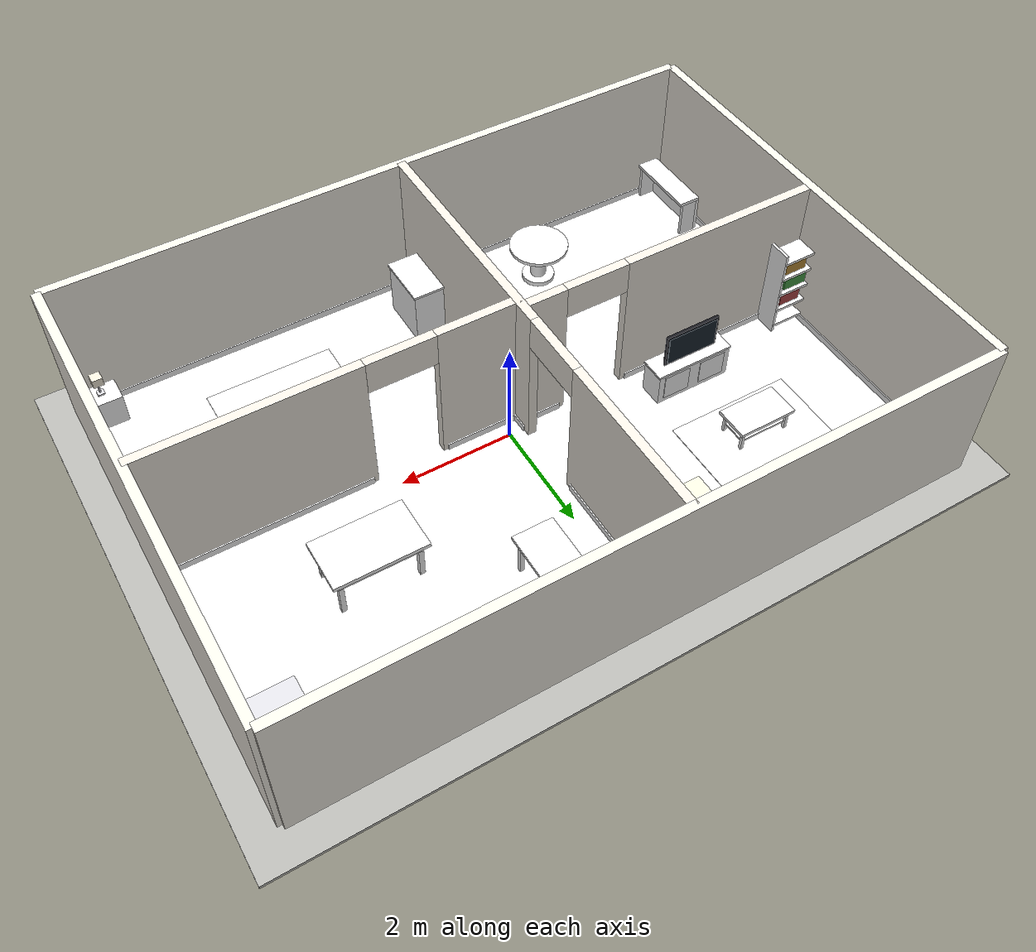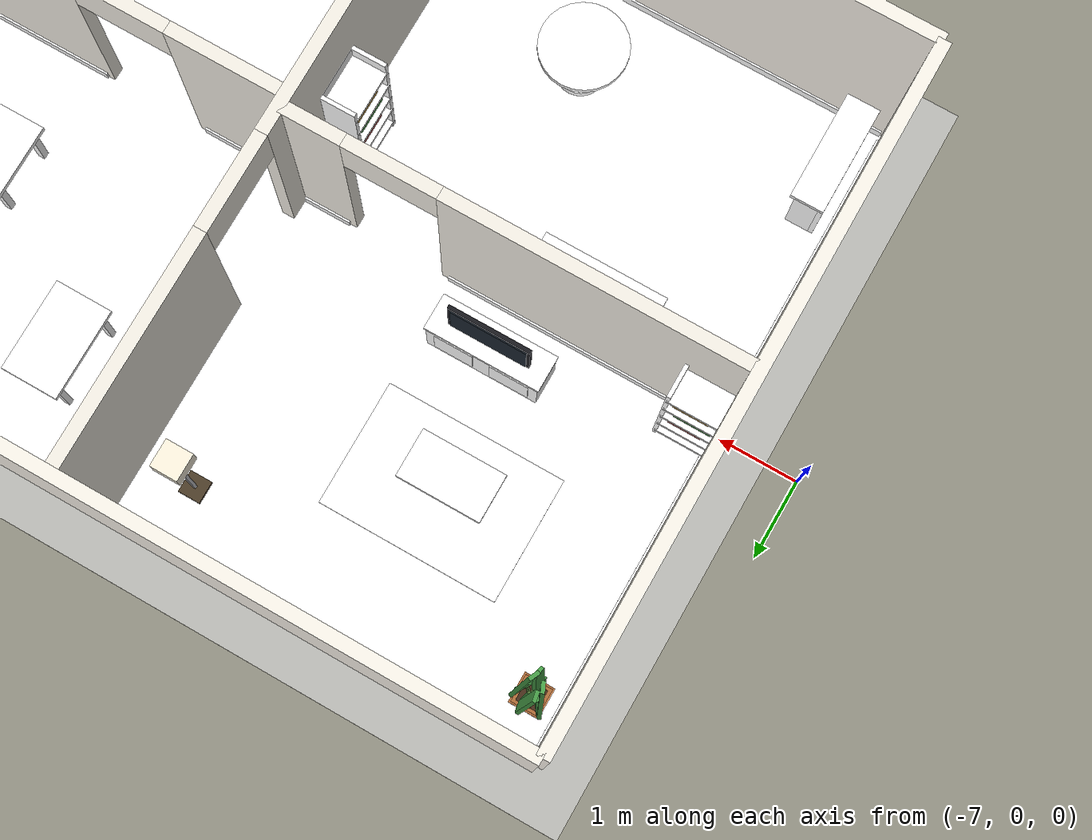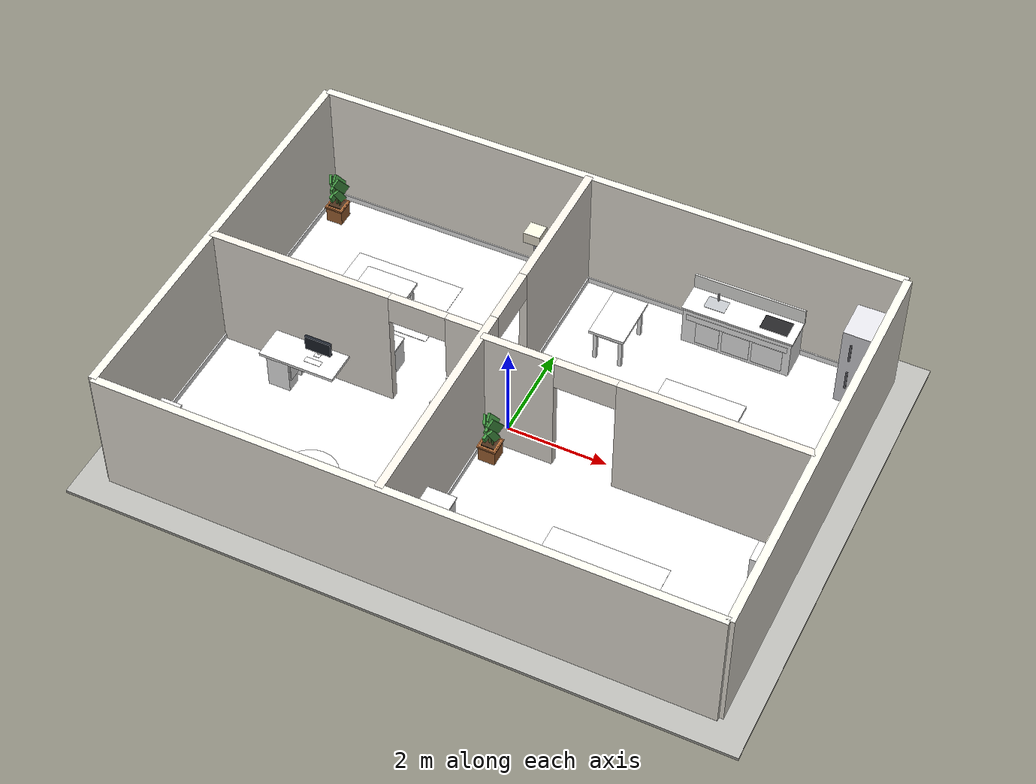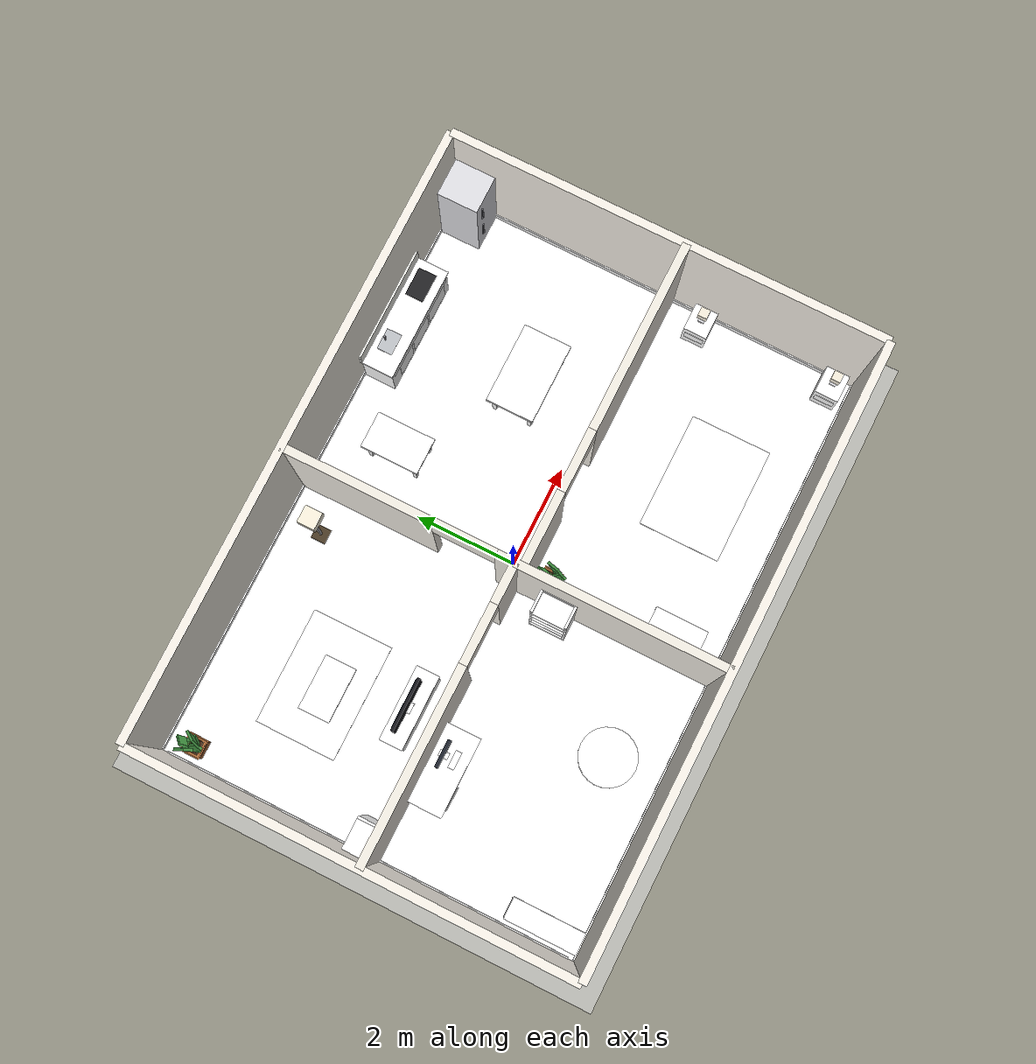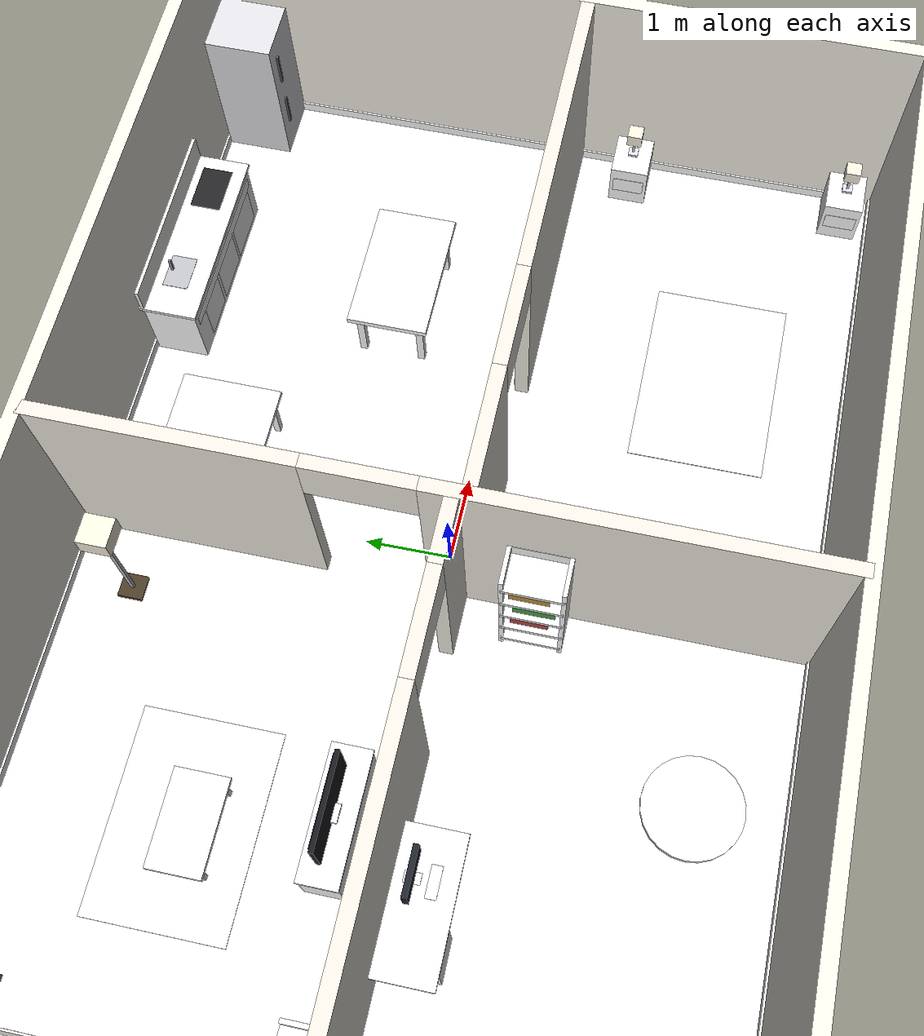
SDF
<sdf version="1.9">
 <world name="house2">
  <include><uri>https://fuel.gazebosim.org/1.0/OpenRobotics/models/Sun</uri></include>
  <gravity>0 0 -9.8</gravity>
  <light name="living_room_light" type="point">
   <pose>-3.40 2.20 2.35 0 0 0</pose>
   <diffuse>1.0 0.92 0.82 1</diffuse>
   <specular>0.18 0.16 0.14 1</specular>
   <attenuation>
    <range>8.0</range>
    <constant>0.6</constant>
    <linear>0.05</linear>
    <quadratic>0.01</quadratic>
   </attenuation>
  </light>
  <light name="kitchen_light" type="point">
   <pose>3.15 2.20 2.35 0 0 0</pose>
   <diffuse>1.0 0.94 0.86 1</diffuse>
   <specular>0.18 0.16 0.14 1</specular>
   <attenuation>
    <range>8.0</range>
    <constant>0.58</constant>
    <linear>0.05</linear>
    <quadratic>0.01</quadratic>
   </attenuation>
  </light>
  <light name="office_light" type="point">
   <pose>-3.60 -2.00 2.35 0 0 0</pose>
   <diffuse>0.96 0.97 1.0 1</diffuse>
   <specular>0.16 0.16 0.18 1</specular>
   <attenuation>
    <range>8.0</range>
    <constant>0.62</constant>
    <linear>0.05</linear>
    <quadratic>0.012</quadratic>
   </attenuation>
  </light>
  <light name="bedroom_light" type="point">
   <pose>3.60 -2.30 2.30 0 0 0</pose>
   <diffuse>0.98 0.92 0.84 1</diffuse>
   <specular>0.18 0.16 0.14 1</specular>
   <attenuation>
    <range>7.0</range>
    <constant>0.64</constant>
    <linear>0.05</linear>
    <quadratic>0.014</quadratic>
   </attenuation>
  </light>
  <include><uri>model://house_shell</uri><name>house_shell</name></include>
  <include><uri>model://rug</uri><name>living_rug</name><pose>-3.55 2.10 0 0 0 0</pose></include>
  <include>
   <uri>model://coffee_table</uri>
   <name>coffee_table_main</name>
   <pose>-3.60 1.95 0 0 0 0</pose>
  </include>
  <include><uri>model://tv_stand</uri><name>tv_stand_main</name><pose>-3.25 0.45 0 0 0 0</pose></include>
  <include><uri>model://bookshelf</uri><name>bookshelf_living</name><pose>-5.64 0.05 0 0 0 1.57</pose></include>
  <include><uri>model://floor_lamp</uri><name>living_lamp</name><pose>-1.10 3.45 0 0 0 0</pose></include>
  <include><uri>model://plant</uri><name>living_plant</name><pose>-5.58 3.62 0 0 0 0</pose></include>
  <include>
   <uri>model://kitchen_counter</uri>
   <name>kitchen_counter_main</name>
   <pose>3.10 3.82 0 0 0 0</pose>
  </include>
  <include><uri>model://fridge</uri><name>fridge_main</name><pose>5.55 3.75 0 0 0 4.71239</pose></include>
  <include><uri>model://table</uri><name>dining_table</name><pose>3.20 1.30 0 0 0 0</pose></include>
  <include>
   <uri>model://small_table</uri>
   <name>kitchen_side_table</name>
   <pose>0.95 2.85 0 0 0 1.57</pose>
  </include>
  <include><uri>model://desk</uri><name>desk_main</name><pose>-3.95 -0.58 0 0 0 0</pose></include>
  <include><uri>model://round_table</uri><name>meeting_table</name><pose>-2.45 -3.10 0 0 0 0</pose></include>
  <include>
   <uri>model://bookshelf</uri>
   <name>bookshelf_office</name>
   <pose>-0.62 -1.10 0 0 0 3.14159</pose>
  </include>
  <include><uri>model://u_desk</uri><name>desk_secondary</name><pose>-5.6 -3.4 0 0 0 0</pose></include>
  <include><uri>model://rug</uri><name>bedroom_rug</name><pose>2.90 -2.55 0 0 0 0</pose></include>
  <include>
   <uri>model://nightstand</uri>
   <name>nightstand_left</name>
   <pose>5.60 -1.10 0 0 0 3.14159</pose>
  </include>
  <include>
   <uri>model://nightstand</uri>
   <name>nightstand_right</name>
   <pose>5.60 -3.80 0 0 0 3.14159</pose>
  </include>
  <include><uri>model://dresser</uri><name>dresser_main</name><pose>-0.04 -3.20 0 0 0 1.57</pose></include>
  <include><uri>model://plant</uri><name>bedroom_plant</name><pose>0.00 -0.75 0 0 0 0</pose></include>
 </world>
</sdf>

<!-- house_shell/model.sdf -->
<sdf version="1.9">
  <model name="house_shell">
    <static>true</static>
    <link name="link">

      <visual name="base_slab_visual">
        <pose>0 0 -0.05 0 0 0</pose>
        <geometry><box><size>13.2 9.7 0.06</size></box></geometry>
        <material>
          <ambient>0.58 0.58 0.57 1</ambient>
          <diffuse>0.72 0.72 0.70 1</diffuse>
        </material>
      </visual>
      <collision name="base_slab_collision">
        <pose>0 0 -0.05 0 0 0</pose>
        <geometry><box><size>13.2 9.7 0.06</size></box></geometry>
      </collision>

      <visual name="floor_visual">
        <pose>0 0 -0.006 0 0 0</pose>
        <geometry><box><size>12.0 8.5 0.012</size></box></geometry>
        <material>
          <ambient>1 1 1 1</ambient>
          <diffuse>1 1 1 1</diffuse>
          <specular>0.05 0.05 0.05 1</specular>
          <pbr>
            <metal>
              <albedo_map>materials/textures/floor_albedo.jpg</albedo_map>
              <normal_map>materials/textures/floor_normal.jpg</normal_map>
              <roughness_map>materials/textures/floor_roughness.jpg</roughness_map>
              <metalness>0.0</metalness>
            </metal>
          </pbr>
        </material>
      </visual>
      <collision name="floor_collision">
        <pose>0 0 -0.006 0 0 0</pose>
        <geometry><box><size>12.0 8.5 0.012</size></box></geometry>
      </collision>

      <visual name="baseboard_west">
        <pose>-5.92 0 0.06 0 0 0</pose>
        <geometry><box><size>0.05 8.10 0.12</size></box></geometry>
        <material><ambient>1 1 1 1</ambient><diffuse>1 1 1 1</diffuse><specular>0.05 0.05 0.05 1</specular><pbr><metal><albedo_map>materials/textures/baseboard_albedo.jpg</albedo_map><normal_map>materials/textures/baseboard_normal.jpg</normal_map><roughness_map>materials/textures/baseboard_roughness.jpg</roughness_map><metalness>0.0</metalness></metal></pbr></material>
      </visual>
      <visual name="baseboard_east">
        <pose>5.92 0 0.06 0 0 0</pose>
        <geometry><box><size>0.05 8.10 0.12</size></box></geometry>
        <material><ambient>1 1 1 1</ambient><diffuse>1 1 1 1</diffuse><specular>0.05 0.05 0.05 1</specular><pbr><metal><albedo_map>materials/textures/baseboard_albedo.jpg</albedo_map><normal_map>materials/textures/baseboard_normal.jpg</normal_map><roughness_map>materials/textures/baseboard_roughness.jpg</roughness_map><metalness>0.0</metalness></metal></pbr></material>
      </visual>
      <visual name="baseboard_north">
        <pose>0 4.17 0.06 0 0 0</pose>
        <geometry><box><size>11.80 0.05 0.12</size></box></geometry>
        <material><ambient>1 1 1 1</ambient><diffuse>1 1 1 1</diffuse><specular>0.05 0.05 0.05 1</specular><pbr><metal><albedo_map>materials/textures/baseboard_albedo.jpg</albedo_map><normal_map>materials/textures/baseboard_normal.jpg</normal_map><roughness_map>materials/textures/baseboard_roughness.jpg</roughness_map><metalness>0.0</metalness></metal></pbr></material>
      </visual>
      <visual name="baseboard_south">
        <pose>0 -4.17 0.06 0 0 0</pose>
        <geometry><box><size>11.80 0.05 0.12</size></box></geometry>
        <material><ambient>1 1 1 1</ambient><diffuse>1 1 1 1</diffuse><specular>0.05 0.05 0.05 1</specular><pbr><metal><albedo_map>materials/textures/baseboard_albedo.jpg</albedo_map><normal_map>materials/textures/baseboard_normal.jpg</normal_map><roughness_map>materials/textures/baseboard_roughness.jpg</roughness_map><metalness>0.0</metalness></metal></pbr></material>
      </visual>
      <visual name="baseboard_mid_lower">
        <pose>-0.27 -2.05 0.06 0 0 0</pose>
        <geometry><box><size>0.05 4.18 0.12</size></box></geometry>
        <material><ambient>1 1 1 1</ambient><diffuse>1 1 1 1</diffuse><specular>0.05 0.05 0.05 1</specular><pbr><metal><albedo_map>materials/textures/baseboard_albedo.jpg</albedo_map><normal_map>materials/textures/baseboard_normal.jpg</normal_map><roughness_map>materials/textures/baseboard_roughness.jpg</roughness_map><metalness>0.0</metalness></metal></pbr></material>
      </visual>
      <visual name="baseboard_mid_upper">
        <pose>-0.27 2.80 0.06 0 0 0</pose>
        <geometry><box><size>0.05 2.68 0.12</size></box></geometry>
        <material><ambient>1 1 1 1</ambient><diffuse>1 1 1 1</diffuse><specular>0.05 0.05 0.05 1</specular><pbr><metal><albedo_map>materials/textures/baseboard_albedo.jpg</albedo_map><normal_map>materials/textures/baseboard_normal.jpg</normal_map><roughness_map>materials/textures/baseboard_roughness.jpg</roughness_map><metalness>0.0</metalness></metal></pbr></material>
      </visual>
      <visual name="baseboard_left_divider_a">
        <pose>-4.14 -0.12 0.06 0 0 0</pose>
        <geometry><box><size>3.55 0.05 0.12</size></box></geometry>
        <material><ambient>1 1 1 1</ambient><diffuse>1 1 1 1</diffuse><specular>0.05 0.05 0.05 1</specular><pbr><metal><albedo_map>materials/textures/baseboard_albedo.jpg</albedo_map><normal_map>materials/textures/baseboard_normal.jpg</normal_map><roughness_map>materials/textures/baseboard_roughness.jpg</roughness_map><metalness>0.0</metalness></metal></pbr></material>
      </visual>
      <visual name="baseboard_left_divider_b">
        <pose>-0.74 -0.12 0.06 0 0 0</pose>
        <geometry><box><size>0.60 0.05 0.12</size></box></geometry>
        <material><ambient>1 1 1 1</ambient><diffuse>1 1 1 1</diffuse><specular>0.05 0.05 0.05 1</specular><pbr><metal><albedo_map>materials/textures/baseboard_albedo.jpg</albedo_map><normal_map>materials/textures/baseboard_normal.jpg</normal_map><roughness_map>materials/textures/baseboard_roughness.jpg</roughness_map><metalness>0.0</metalness></metal></pbr></material>
      </visual>
      <visual name="baseboard_right_divider_a">
        <pose>0.38 -0.27 0.06 0 0 0</pose>
        <geometry><box><size>1.28 0.05 0.12</size></box></geometry>
        <material><ambient>1 1 1 1</ambient><diffuse>1 1 1 1</diffuse><specular>0.05 0.05 0.05 1</specular><pbr><metal><albedo_map>materials/textures/baseboard_albedo.jpg</albedo_map><normal_map>materials/textures/baseboard_normal.jpg</normal_map><roughness_map>materials/textures/baseboard_roughness.jpg</roughness_map><metalness>0.0</metalness></metal></pbr></material>
      </visual>
      <visual name="baseboard_right_divider_b">
        <pose>4.15 -0.27 0.06 0 0 0</pose>
        <geometry><box><size>3.54 0.05 0.12</size></box></geometry>
        <material><ambient>1 1 1 1</ambient><diffuse>1 1 1 1</diffuse><specular>0.05 0.05 0.05 1</specular><pbr><metal><albedo_map>materials/textures/baseboard_albedo.jpg</albedo_map><normal_map>materials/textures/baseboard_normal.jpg</normal_map><roughness_map>materials/textures/baseboard_roughness.jpg</roughness_map><metalness>0.0</metalness></metal></pbr></material>
      </visual>

      <!-- outer walls -->
      <collision name="wall_west">
        <pose>-6.0 0.0 1.35 0 0 0</pose>
        <geometry><box><size>0.16 8.5 2.7</size></box></geometry>
      </collision>
      <visual name="wall_west_visual">
        <pose>-6.0 0.0 1.35 0 0 0</pose>
        <geometry><box><size>0.16 8.5 2.7</size></box></geometry>
        <material><ambient>0.90 0.88 0.84 1</ambient><diffuse>0.97 0.95 0.91 1</diffuse></material>
      </visual>

      <collision name="wall_east">
        <pose>6.0 0.0 1.35 0 0 0</pose>
        <geometry><box><size>0.16 8.5 2.7</size></box></geometry>
      </collision>
      <visual name="wall_east_visual">
        <pose>6.0 0.0 1.35 0 0 0</pose>
        <geometry><box><size>0.16 8.5 2.7</size></box></geometry>
        <material><ambient>0.90 0.88 0.84 1</ambient><diffuse>0.97 0.95 0.91 1</diffuse></material>
      </visual>

      <collision name="wall_north">
        <pose>0.0 4.25 1.35 0 0 0</pose>
        <geometry><box><size>12.0 0.16 2.7</size></box></geometry>
      </collision>
      <visual name="wall_north_visual">
        <pose>0.0 4.25 1.35 0 0 0</pose>
        <geometry><box><size>12.0 0.16 2.7</size></box></geometry>
        <material><ambient>0.90 0.88 0.84 1</ambient><diffuse>0.97 0.95 0.91 1</diffuse></material>
      </visual>

      <collision name="wall_south">
        <pose>0.0 -4.25 1.35 0 0 0</pose>
        <geometry><box><size>12.0 0.16 2.7</size></box></geometry>
      </collision>
      <visual name="wall_south_visual">
        <pose>0.0 -4.25 1.35 0 0 0</pose>
        <geometry><box><size>12.0 0.16 2.7</size></box></geometry>
        <material><ambient>0.90 0.88 0.84 1</ambient><diffuse>0.97 0.95 0.91 1</diffuse></material>
      </visual>

      <!-- center hall wall -->
      <collision name="mid_wall_bottom">
        <pose>-0.35 -2.05 1.35 0 0 0</pose>
        <geometry><box><size>0.16 4.40 2.7</size></box></geometry>
      </collision>
      <visual name="mid_wall_bottom_visual">
        <pose>-0.35 -2.05 1.35 0 0 0</pose>
        <geometry><box><size>0.16 4.40 2.7</size></box></geometry>
        <material><ambient>0.88 0.86 0.82 1</ambient><diffuse>0.95 0.93 0.89 1</diffuse></material>
      </visual>

      <collision name="mid_wall_top">
        <pose>-0.35 2.80 1.35 0 0 0</pose>
        <geometry><box><size>0.16 2.90 2.7</size></box></geometry>
      </collision>
      <visual name="mid_wall_top_visual">
        <pose>-0.35 2.80 1.35 0 0 0</pose>
        <geometry><box><size>0.16 2.90 2.7</size></box></geometry>
        <material><ambient>0.88 0.86 0.82 1</ambient><diffuse>0.95 0.93 0.89 1</diffuse></material>
      </visual>

      <collision name="mid_door_header">
        <pose>-0.35 0.75 2.40 0 0 0</pose>
        <geometry><box><size>0.16 1.20 0.60</size></box></geometry>
      </collision>
      <visual name="mid_door_header_visual">
        <pose>-0.35 0.75 2.40 0 0 0</pose>
        <geometry><box><size>0.16 1.20 0.60</size></box></geometry>
        <material><ambient>0.88 0.86 0.82 1</ambient><diffuse>0.95 0.93 0.89 1</diffuse></material>
      </visual>

      <!-- left-side room divider -->
      <collision name="left_divider_left">
        <pose>-4.1375 -0.20 1.35 0 0 0</pose>
        <geometry><box><size>3.725 0.16 2.7</size></box></geometry>
      </collision>
      <visual name="left_divider_left_visual">
        <pose>-4.1375 -0.20 1.35 0 0 0</pose>
        <geometry><box><size>3.725 0.16 2.7</size></box></geometry>
        <material><ambient>0.88 0.86 0.82 1</ambient><diffuse>0.95 0.93 0.89 1</diffuse></material>
      </visual>

      <collision name="left_divider_right">
        <pose>-0.7375 -0.20 1.35 0 0 0</pose>
        <geometry><box><size>0.775 0.16 2.7</size></box></geometry>
      </collision>
      <visual name="left_divider_right_visual">
        <pose>-0.7375 -0.20 1.35 0 0 0</pose>
        <geometry><box><size>0.775 0.16 2.7</size></box></geometry>
        <material><ambient>0.88 0.86 0.82 1</ambient><diffuse>0.95 0.93 0.89 1</diffuse></material>
      </visual>

      <collision name="left_door_header">
        <pose>-1.70 -0.20 2.40 0 0 0</pose>
        <geometry><box><size>1.15 0.16 0.60</size></box></geometry>
      </collision>
      <visual name="left_door_header_visual">
        <pose>-1.70 -0.20 2.40 0 0 0</pose>
        <geometry><box><size>1.15 0.16 0.60</size></box></geometry>
        <material><ambient>0.88 0.86 0.82 1</ambient><diffuse>0.95 0.93 0.89 1</diffuse></material>
      </visual>

      <!-- bedroom divider -->
      <collision name="right_divider_left">
        <pose>0.375 -0.35 1.35 0 0 0</pose>
        <geometry><box><size>1.45 0.16 2.7</size></box></geometry>
      </collision>
      <visual name="right_divider_left_visual">
        <pose>0.375 -0.35 1.35 0 0 0</pose>
        <geometry><box><size>1.45 0.16 2.7</size></box></geometry>
        <material><ambient>0.88 0.86 0.82 1</ambient><diffuse>0.95 0.93 0.89 1</diffuse></material>
      </visual>

      <collision name="right_divider_right">
        <pose>4.15 -0.35 1.35 0 0 0</pose>
        <geometry><box><size>3.70 0.16 2.7</size></box></geometry>
      </collision>
      <visual name="right_divider_right_visual">
        <pose>4.15 -0.35 1.35 0 0 0</pose>
        <geometry><box><size>3.70 0.16 2.7</size></box></geometry>
        <material><ambient>0.88 0.86 0.82 1</ambient><diffuse>0.95 0.93 0.89 1</diffuse></material>
      </visual>

      <collision name="right_door_header">
        <pose>1.70 -0.35 2.40 0 0 0</pose>
        <geometry><box><size>1.20 0.16 0.60</size></box></geometry>
      </collision>
      <visual name="right_door_header_visual">
        <pose>1.70 -0.35 2.40 0 0 0</pose>
        <geometry><box><size>1.20 0.16 0.60</size></box></geometry>
        <material><ambient>0.88 0.86 0.82 1</ambient><diffuse>0.95 0.93 0.89 1</diffuse></material>
      </visual>

    </link>
  </model>
</sdf>

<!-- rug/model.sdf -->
<sdf version="1.9">
  <model name="rug">
    <static>true</static>
    <link name="body">

      <visual name="rug_base">
        <pose>0 0 0.005 0 0 0</pose>
        <geometry><box><size>2.30 1.60 0.01</size></box></geometry>
        <material>
          <ambient>1 1 1 1</ambient>
          <diffuse>1 1 1 1</diffuse>
          <specular>0.01 0.01 0.01 1</specular>
          <pbr>
            <metal>
              <albedo_map>materials/textures/carpet_albedo.jpg</albedo_map>
              <normal_map>materials/textures/carpet_normal.jpg</normal_map>
              <roughness_map>materials/textures/carpet_roughness.jpg</roughness_map>
              <metalness>0.0</metalness>
            </metal>
          </pbr>
        </material>
      </visual>
    </link>
  </model>
</sdf>

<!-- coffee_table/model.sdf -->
<sdf version="1.9">
  <model name="coffee_table">
    <static>true</static>
    <link name="body">

      <collision name="top_collision">
        <pose>0 0 0.42 0 0 0</pose>
        <geometry><box><size>1.08 0.62 0.06</size></box></geometry>
      </collision>
      <visual name="top_visual">
        <pose>0 0 0.42 0 0 0</pose>
        <geometry><box><size>1.08 0.62 0.06</size></box></geometry>
        <material>
          <ambient>1 1 1 1</ambient>
          <diffuse>1 1 1 1</diffuse>
          <specular>0.05 0.05 0.05 1</specular>
          <pbr>
            <metal>
              <albedo_map>materials/textures/wood_albedo.png</albedo_map>
              <normal_map>materials/textures/wood_normal.png</normal_map>
              <roughness_map>materials/textures/wood_roughness.png</roughness_map>
              <metalness>0.0</metalness>
            </metal>
          </pbr>
        </material>
      </visual>

      <collision name="shelf_collision">
        <pose>0 0 0.17 0 0 0</pose>
        <geometry><box><size>0.90 0.46 0.035</size></box></geometry>
      </collision>
      <visual name="shelf_visual">
        <pose>0 0 0.17 0 0 0</pose>
        <geometry><box><size>0.90 0.46 0.035</size></box></geometry>
        <material>
          <ambient>1 1 1 1</ambient>
          <diffuse>1 1 1 1</diffuse>
          <specular>0.05 0.05 0.05 1</specular>
          <pbr>
            <metal>
              <albedo_map>materials/textures/wood_albedo.png</albedo_map>
              <normal_map>materials/textures/wood_normal.png</normal_map>
              <roughness_map>materials/textures/wood_roughness.png</roughness_map>
              <metalness>0.0</metalness>
            </metal>
          </pbr>
        </material>
      </visual>

      <collision name="leg_fl">
        <pose>0.45 0.23 0.21 0 0 0</pose>
        <geometry><box><size>0.055 0.055 0.43</size></box></geometry>
      </collision>
      <collision name="leg_fr">
        <pose>0.45 -0.23 0.21 0 0 0</pose>
        <geometry><box><size>0.055 0.055 0.43</size></box></geometry>
      </collision>
      <collision name="leg_bl">
        <pose>-0.45 0.23 0.21 0 0 0</pose>
        <geometry><box><size>0.055 0.055 0.43</size></box></geometry>
      </collision>
      <collision name="leg_br">
        <pose>-0.45 -0.23 0.21 0 0 0</pose>
        <geometry><box><size>0.055 0.055 0.43</size></box></geometry>
      </collision>

      <visual name="leg_fl_visual">
        <pose>0.45 0.23 0.21 0 0 0</pose>
        <geometry><box><size>0.055 0.055 0.43</size></box></geometry>
        <material><ambient>1 1 1 1</ambient><diffuse>1 1 1 1</diffuse><specular>0.05 0.05 0.05 1</specular><pbr><metal><albedo_map>materials/textures/wood_albedo.png</albedo_map><normal_map>materials/textures/wood_normal.png</normal_map><roughness_map>materials/textures/wood_roughness.png</roughness_map><metalness>0.0</metalness></metal></pbr></material>
      </visual>
      <visual name="leg_fr_visual">
        <pose>0.45 -0.23 0.21 0 0 0</pose>
        <geometry><box><size>0.055 0.055 0.43</size></box></geometry>
        <material><ambient>1 1 1 1</ambient><diffuse>1 1 1 1</diffuse><specular>0.05 0.05 0.05 1</specular><pbr><metal><albedo_map>materials/textures/wood_albedo.png</albedo_map><normal_map>materials/textures/wood_normal.png</normal_map><roughness_map>materials/textures/wood_roughness.png</roughness_map><metalness>0.0</metalness></metal></pbr></material>
      </visual>
      <visual name="leg_bl_visual">
        <pose>-0.45 0.23 0.21 0 0 0</pose>
        <geometry><box><size>0.055 0.055 0.43</size></box></geometry>
        <material><ambient>1 1 1 1</ambient><diffuse>1 1 1 1</diffuse><specular>0.05 0.05 0.05 1</specular><pbr><metal><albedo_map>materials/textures/wood_albedo.png</albedo_map><normal_map>materials/textures/wood_normal.png</normal_map><roughness_map>materials/textures/wood_roughness.png</roughness_map><metalness>0.0</metalness></metal></pbr></material>
      </visual>
      <visual name="leg_br_visual">
        <pose>-0.45 -0.23 0.21 0 0 0</pose>
        <geometry><box><size>0.055 0.055 0.43</size></box></geometry>
        <material><ambient>1 1 1 1</ambient><diffuse>1 1 1 1</diffuse><specular>0.05 0.05 0.05 1</specular><pbr><metal><albedo_map>materials/textures/wood_albedo.png</albedo_map><normal_map>materials/textures/wood_normal.png</normal_map><roughness_map>materials/textures/wood_roughness.png</roughness_map><metalness>0.0</metalness></metal></pbr></material>
      </visual>

    </link>
  </model>
</sdf>

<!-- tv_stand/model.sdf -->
<sdf version="1.9">
  <model name="tv_stand">
    <static>true</static>
    <link name="body">

      <collision name="cabinet_collision">
        <pose>0 0 0.31 0 0 0</pose>
        <geometry><box><size>1.44 0.44 0.64</size></box></geometry>
      </collision>
      <collision name="top_slab_collision">
        <pose>0 0 0.63 0 0 0</pose>
        <geometry><box><size>1.48 0.46 0.04</size></box></geometry>
      </collision>
      <collision name="center_shelf_collision">
        <pose>0 0 0.28 0 0 0</pose>
        <geometry><box><size>0.34 0.36 0.03</size></box></geometry>
      </collision>
      <collision name="left_door_collision">
        <pose>-0.36 0.22 0.33 0 0 0</pose>
        <geometry><box><size>0.50 0.03 0.48</size></box></geometry>
      </collision>
      <collision name="right_door_collision">
        <pose>0.36 0.22 0.33 0 0 0</pose>
        <geometry><box><size>0.50 0.03 0.48</size></box></geometry>
      </collision>
      <collision name="tv_collision">
        <pose>0 0.03 1.00 0 0 0</pose>
        <geometry><box><size>1.04 0.05 0.64</size></box></geometry>
      </collision>
      <collision name="tv_base_collision">
        <pose>0 0 0.76 0 0 0</pose>
        <geometry><box><size>0.20 0.12 0.04</size></box></geometry>
      </collision>
      <visual name="cabinet_visual">
        <pose>0 0 0.31 0 0 0</pose>
        <geometry><box><size>1.44 0.44 0.64</size></box></geometry>
        <material>
          <ambient>1 1 1 1</ambient>
          <diffuse>1 1 1 1</diffuse>
          <specular>0.05 0.05 0.05 1</specular>
          <pbr>
            <metal>
              <albedo_map>materials/textures/wood_albedo.jpg</albedo_map>
              <normal_map>materials/textures/wood_normal.jpg</normal_map>
              <roughness_map>materials/textures/wood_roughness.jpg</roughness_map>
              <metalness>0.0</metalness>
            </metal>
          </pbr>
        </material>
      </visual>

      <visual name="top_slab">
        <pose>0 0 0.63 0 0 0</pose>
        <geometry><box><size>1.48 0.46 0.04</size></box></geometry>
        <material><ambient>1 1 1 1</ambient><diffuse>1 1 1 1</diffuse><specular>0.05 0.05 0.05 1</specular><pbr><metal><albedo_map>materials/textures/wood_albedo.jpg</albedo_map><normal_map>materials/textures/wood_normal.jpg</normal_map><roughness_map>materials/textures/wood_roughness.jpg</roughness_map><metalness>0.0</metalness></metal></pbr></material>
      </visual>

      <visual name="left_door">
        <pose>-0.36 0.22 0.33 0 0 0</pose>
        <geometry><box><size>0.50 0.03 0.48</size></box></geometry>
        <material><ambient>1 1 1 1</ambient><diffuse>1 1 1 1</diffuse><specular>0.05 0.05 0.05 1</specular><pbr><metal><albedo_map>materials/textures/wood_albedo.jpg</albedo_map><normal_map>materials/textures/wood_normal.jpg</normal_map><roughness_map>materials/textures/wood_roughness.jpg</roughness_map><metalness>0.0</metalness></metal></pbr></material>
      </visual>
      <visual name="right_door">
        <pose>0.36 0.22 0.33 0 0 0</pose>
        <geometry><box><size>0.50 0.03 0.48</size></box></geometry>
        <material><ambient>1 1 1 1</ambient><diffuse>1 1 1 1</diffuse><specular>0.05 0.05 0.05 1</specular><pbr><metal><albedo_map>materials/textures/wood_albedo.jpg</albedo_map><normal_map>materials/textures/wood_normal.jpg</normal_map><roughness_map>materials/textures/wood_roughness.jpg</roughness_map><metalness>0.0</metalness></metal></pbr></material>
      </visual>
      <visual name="center_shelf">
        <pose>0 0 0.28 0 0 0</pose>
        <geometry><box><size>0.34 0.36 0.03</size></box></geometry>
        <material><ambient>1 1 1 1</ambient><diffuse>1 1 1 1</diffuse><specular>0.05 0.05 0.05 1</specular><pbr><metal><albedo_map>materials/textures/wood_albedo.jpg</albedo_map><normal_map>materials/textures/wood_normal.jpg</normal_map><roughness_map>materials/textures/wood_roughness.jpg</roughness_map><metalness>0.0</metalness></metal></pbr></material>
      </visual>

      <visual name="tv_frame">
        <pose>0 0.03 1.00 0 0 0</pose>
        <geometry><box><size>1.04 0.05 0.64</size></box></geometry>
        <material><ambient>0.05 0.05 0.06 1</ambient><diffuse>0.10 0.10 0.12 1</diffuse></material>
      </visual>
      <visual name="tv_screen">
        <pose>0 0.06 1.00 0 0 0</pose>
        <geometry><box><size>0.96 0.02 0.56</size></box></geometry>
        <material><ambient>0.05 0.07 0.09 1</ambient><diffuse>0.10 0.14 0.18 1</diffuse></material>
      </visual>
      <visual name="tv_base">
        <pose>0 0 0.76 0 0 0</pose>
        <geometry><box><size>0.20 0.12 0.04</size></box></geometry>
        <material><ambient>1 1 1 1</ambient><diffuse>1 1 1 1</diffuse><specular>0.12 0.12 0.12 1</specular><pbr><metal><albedo_map>materials/textures/metal_albedo.jpg</albedo_map><normal_map>materials/textures/metal_normal.jpg</normal_map><roughness_map>materials/textures/metal_roughness.jpg</roughness_map><metalness_map>materials/textures/metal_metalness.jpg</metalness_map></metal></pbr></material>
      </visual>

    </link>
  </model>
</sdf>

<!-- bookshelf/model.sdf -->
<sdf version="1.9">
  <model name="bookshelf">
    <static>true</static>
    <link name="body">

      <collision name="left_side_collision">
        <pose>0 0.33 0.88 0 0 0</pose>
        <geometry><box><size>0.48 0.05 1.78</size></box></geometry>
      </collision>
      <collision name="right_side_collision">
        <pose>0 -0.33 0.88 0 0 0</pose>
        <geometry><box><size>0.48 0.05 1.78</size></box></geometry>
      </collision>
      <collision name="back_collision">
        <pose>-0.21 0 0.88 0 0 0</pose>
        <geometry><box><size>0.05 0.68 1.78</size></box></geometry>
      </collision>

      <collision name="bottom_shelf_collision">
        <pose>0.03 0 0.14 0 0 0</pose>
        <geometry><box><size>0.44 0.68 0.05</size></box></geometry>
      </collision>
      <collision name="mid1_shelf_collision">
        <pose>0.03 0 0.50 0 0 0</pose>
        <geometry><box><size>0.44 0.68 0.05</size></box></geometry>
      </collision>
      <collision name="mid2_shelf_collision">
        <pose>0.03 0 0.86 0 0 0</pose>
        <geometry><box><size>0.44 0.68 0.05</size></box></geometry>
      </collision>
      <collision name="mid3_shelf_collision">
        <pose>0.03 0 1.22 0 0 0</pose>
        <geometry><box><size>0.44 0.68 0.05</size></box></geometry>
      </collision>
      <collision name="top_shelf_collision">
        <pose>0.03 0 1.58 0 0 0</pose>
        <geometry><box><size>0.44 0.68 0.05</size></box></geometry>
      </collision>

      <collision name="books_2_collision">
        <pose>0.09 -0.03 0.66 0 0 0</pose>
        <geometry><box><size>0.20 0.42 0.24</size></box></geometry>
      </collision>
      <collision name="books_3_collision">
        <pose>0.09 0.02 1.02 0 0 0</pose>
        <geometry><box><size>0.20 0.46 0.24</size></box></geometry>
      </collision>
      <collision name="books_4_collision">
        <pose>0.09 -0.04 1.38 0 0 0</pose>
        <geometry><box><size>0.20 0.44 0.22</size></box></geometry>
      </collision>

      <visual name="left_side_visual">
        <pose>0 0.33 0.88 0 0 0</pose>
        <geometry><box><size>0.48 0.05 1.78</size></box></geometry>
        <material><ambient>1 1 1 1</ambient><diffuse>1 1 1 1</diffuse><specular>0.05 0.05 0.05 1</specular><pbr><metal><albedo_map>materials/textures/wood_albedo.jpg</albedo_map><normal_map>materials/textures/wood_normal.jpg</normal_map><roughness_map>materials/textures/wood_roughness.jpg</roughness_map><metalness>0.0</metalness></metal></pbr></material>
      </visual>
      <visual name="right_side_visual">
        <pose>0 -0.33 0.88 0 0 0</pose>
        <geometry><box><size>0.48 0.05 1.78</size></box></geometry>
        <material><ambient>1 1 1 1</ambient><diffuse>1 1 1 1</diffuse><specular>0.05 0.05 0.05 1</specular><pbr><metal><albedo_map>materials/textures/wood_albedo.jpg</albedo_map><normal_map>materials/textures/wood_normal.jpg</normal_map><roughness_map>materials/textures/wood_roughness.jpg</roughness_map><metalness>0.0</metalness></metal></pbr></material>
      </visual>
      <visual name="back_visual">
        <pose>-0.21 0 0.88 0 0 0</pose>
        <geometry><box><size>0.05 0.68 1.78</size></box></geometry>
        <material><ambient>1 1 1 1</ambient><diffuse>1 1 1 1</diffuse><specular>0.05 0.05 0.05 1</specular><pbr><metal><albedo_map>materials/textures/wood_albedo.jpg</albedo_map><normal_map>materials/textures/wood_normal.jpg</normal_map><roughness_map>materials/textures/wood_roughness.jpg</roughness_map><metalness>0.0</metalness></metal></pbr></material>
      </visual>

      <visual name="bottom_shelf_visual">
        <pose>0.03 0 0.14 0 0 0</pose>
        <geometry><box><size>0.44 0.68 0.05</size></box></geometry>
        <material><ambient>1 1 1 1</ambient><diffuse>1 1 1 1</diffuse><specular>0.05 0.05 0.05 1</specular><pbr><metal><albedo_map>materials/textures/wood_albedo.jpg</albedo_map><normal_map>materials/textures/wood_normal.jpg</normal_map><roughness_map>materials/textures/wood_roughness.jpg</roughness_map><metalness>0.0</metalness></metal></pbr></material>
      </visual>
      <visual name="mid1_shelf_visual">
        <pose>0.03 0 0.50 0 0 0</pose>
        <geometry><box><size>0.44 0.68 0.05</size></box></geometry>
        <material><ambient>1 1 1 1</ambient><diffuse>1 1 1 1</diffuse><specular>0.05 0.05 0.05 1</specular><pbr><metal><albedo_map>materials/textures/wood_albedo.jpg</albedo_map><normal_map>materials/textures/wood_normal.jpg</normal_map><roughness_map>materials/textures/wood_roughness.jpg</roughness_map><metalness>0.0</metalness></metal></pbr></material>
      </visual>
      <visual name="mid2_shelf_visual">
        <pose>0.03 0 0.86 0 0 0</pose>
        <geometry><box><size>0.44 0.68 0.05</size></box></geometry>
        <material><ambient>1 1 1 1</ambient><diffuse>1 1 1 1</diffuse><specular>0.05 0.05 0.05 1</specular><pbr><metal><albedo_map>materials/textures/wood_albedo.jpg</albedo_map><normal_map>materials/textures/wood_normal.jpg</normal_map><roughness_map>materials/textures/wood_roughness.jpg</roughness_map><metalness>0.0</metalness></metal></pbr></material>
      </visual>
      <visual name="mid3_shelf_visual">
        <pose>0.03 0 1.22 0 0 0</pose>
        <geometry><box><size>0.44 0.68 0.05</size></box></geometry>
        <material><ambient>1 1 1 1</ambient><diffuse>1 1 1 1</diffuse><specular>0.05 0.05 0.05 1</specular><pbr><metal><albedo_map>materials/textures/wood_albedo.jpg</albedo_map><normal_map>materials/textures/wood_normal.jpg</normal_map><roughness_map>materials/textures/wood_roughness.jpg</roughness_map><metalness>0.0</metalness></metal></pbr></material>
      </visual>
      <visual name="top_shelf_visual">
        <pose>0.03 0 1.58 0 0 0</pose>
        <geometry><box><size>0.44 0.68 0.05</size></box></geometry>
        <material><ambient>1 1 1 1</ambient><diffuse>1 1 1 1</diffuse><specular>0.05 0.05 0.05 1</specular><pbr><metal><albedo_map>materials/textures/wood_albedo.jpg</albedo_map><normal_map>materials/textures/wood_normal.jpg</normal_map><roughness_map>materials/textures/wood_roughness.jpg</roughness_map><metalness>0.0</metalness></metal></pbr></material>
      </visual>

      <!-- simple books -->
      <visual name="books_2">
        <pose>0.09 -0.03 0.66 0 0 0</pose>
        <geometry><box><size>0.20 0.42 0.24</size></box></geometry>
        <material><ambient>0.45 0.18 0.18 1</ambient><diffuse>0.70 0.28 0.28 1</diffuse></material>
      </visual>
      <visual name="books_3">
        <pose>0.09 0.02 1.02 0 0 0</pose>
        <geometry><box><size>0.20 0.46 0.24</size></box></geometry>
        <material><ambient>0.18 0.40 0.18 1</ambient><diffuse>0.28 0.62 0.28 1</diffuse></material>
      </visual>
      <visual name="books_4">
        <pose>0.09 -0.04 1.38 0 0 0</pose>
        <geometry><box><size>0.20 0.44 0.22</size></box></geometry>
        <material><ambient>0.48 0.36 0.14 1</ambient><diffuse>0.74 0.56 0.22 1</diffuse></material>
      </visual>

    </link>
  </model>
</sdf>

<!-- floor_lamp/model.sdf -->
<sdf version="1.9">
  <model name="floor_lamp">
    <static>true</static>
    <link name="body">

      <collision name="base_collision">
        <pose>0 0 0.03 0 0 0</pose>
        <geometry><box><size>0.28 0.28 0.06</size></box></geometry>
      </collision>
      <collision name="stem_collision">
        <pose>0 0 0.80 0 0 0</pose>
        <geometry><box><size>0.04 0.04 1.50</size></box></geometry>
      </collision>
      <collision name="shade_collision">
        <pose>0 0 1.55 0 0 0</pose>
        <geometry><box><size>0.34 0.34 0.24</size></box></geometry>
      </collision>
      <visual name="base_visual">
        <pose>0 0 0.03 0 0 0</pose>
        <geometry><box><size>0.28 0.28 0.06</size></box></geometry>
        <material>
          <ambient>0.20 0.16 0.11 1</ambient>
          <diffuse>0.30 0.24 0.16 1</diffuse>
        </material>
      </visual>

      <visual name="stem_visual">
        <pose>0 0 0.80 0 0 0</pose>
        <geometry><box><size>0.04 0.04 1.50</size></box></geometry>
        <material><ambient>0.62 0.62 0.63 1</ambient><diffuse>0.78 0.78 0.80 1</diffuse></material>
      </visual>
      <visual name="shade_visual">
        <pose>0 0 1.55 0 0 0</pose>
        <geometry><box><size>0.34 0.34 0.24</size></box></geometry>
        <material><ambient>0.92 0.89 0.80 1</ambient><diffuse>0.98 0.95 0.87 1</diffuse></material>
      </visual>

    </link>
  </model>
</sdf>

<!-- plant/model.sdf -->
<sdf version="1.9">
  <model name="plant">
    <static>true</static>
    <link name="body">

      <collision name="pot_collision">
        <pose>0 0 0.18 0 0 0</pose>
        <geometry><box><size>0.34 0.34 0.38</size></box></geometry>
      </collision>
      <collision name="pot_lip_collision">
        <pose>0 0 0.35 0 0 0</pose>
        <geometry><box><size>0.38 0.38 0.03</size></box></geometry>
      </collision>
      <collision name="stem_main_collision">
        <pose>0 0 0.64 0 0 0</pose>
        <geometry><box><size>0.04 0.04 0.52</size></box></geometry>
      </collision>
      <collision name="stem_left_collision">
        <pose>-0.06 0.02 0.58 0.18 0.14 0</pose>
        <geometry><box><size>0.03 0.03 0.34</size></box></geometry>
      </collision>
      <collision name="stem_right_collision">
        <pose>0.06 -0.02 0.58 -0.18 -0.14 0</pose>
        <geometry><box><size>0.03 0.03 0.34</size></box></geometry>
      </collision>
      <collision name="leaf_left_top_collision">
        <pose>-0.12 0.03 0.92 0.65 0 0.40</pose>
        <geometry><box><size>0.05 0.18 0.42</size></box></geometry>
      </collision>
      <collision name="leaf_right_top_collision">
        <pose>0.12 -0.03 0.92 0.65 0 -0.40</pose>
        <geometry><box><size>0.05 0.18 0.42</size></box></geometry>
      </collision>
      <collision name="leaf_front_top_collision">
        <pose>0 0.12 0.88 0.52 -0.34 0</pose>
        <geometry><box><size>0.05 0.16 0.36</size></box></geometry>
      </collision>
      <collision name="leaf_back_top_collision">
        <pose>0 -0.12 0.88 0.52 0.34 0</pose>
        <geometry><box><size>0.05 0.16 0.36</size></box></geometry>
      </collision>
      <collision name="leaf_left_low_collision">
        <pose>-0.10 0.06 0.68 0.48 0 0.62</pose>
        <geometry><box><size>0.05 0.15 0.30</size></box></geometry>
      </collision>
      <collision name="leaf_right_low_collision">
        <pose>0.10 -0.06 0.68 0.48 0 -0.62</pose>
        <geometry><box><size>0.05 0.15 0.30</size></box></geometry>
      </collision>
      <collision name="leaf_front_low_collision">
        <pose>0.03 0.11 0.62 0.42 -0.22 0.15</pose>
        <geometry><box><size>0.05 0.14 0.26</size></box></geometry>
      </collision>
      <collision name="leaf_back_low_collision">
        <pose>-0.03 -0.11 0.62 0.42 0.22 -0.15</pose>
        <geometry><box><size>0.05 0.14 0.26</size></box></geometry>
      </collision>
      <visual name="pot_visual">
        <pose>0 0 0.18 0 0 0</pose>
        <geometry><box><size>0.34 0.34 0.38</size></box></geometry>
        <material>
          <ambient>0.50 0.31 0.16 1</ambient>
          <diffuse>0.68 0.42 0.22 1</diffuse>
        </material>
      </visual>
      <visual name="pot_lip">
        <pose>0 0 0.35 0 0 0</pose>
        <geometry><box><size>0.38 0.38 0.03</size></box></geometry>
        <material><ambient>0.56 0.35 0.18 1</ambient><diffuse>0.74 0.46 0.25 1</diffuse></material>
      </visual>
      <visual name="soil_visual">
        <pose>0 0 0.38 0 0 0</pose>
        <geometry><box><size>0.26 0.26 0.03</size></box></geometry>
        <material><ambient>0.19 0.12 0.07 1</ambient><diffuse>0.28 0.18 0.10 1</diffuse></material>
      </visual>

      <visual name="stem_main">
        <pose>0 0 0.64 0 0 0</pose>
        <geometry><box><size>0.04 0.04 0.52</size></box></geometry>
        <material><ambient>0.22 0.33 0.15 1</ambient><diffuse>0.34 0.50 0.22 1</diffuse></material>
      </visual>
      <visual name="stem_left">
        <pose>-0.06 0.02 0.58 0.18 0.14 0</pose>
        <geometry><box><size>0.03 0.03 0.34</size></box></geometry>
        <material><ambient>0.22 0.33 0.15 1</ambient><diffuse>0.34 0.50 0.22 1</diffuse></material>
      </visual>
      <visual name="stem_right">
        <pose>0.06 -0.02 0.58 -0.18 -0.14 0</pose>
        <geometry><box><size>0.03 0.03 0.34</size></box></geometry>
        <material><ambient>0.22 0.33 0.15 1</ambient><diffuse>0.34 0.50 0.22 1</diffuse></material>
      </visual>

      <visual name="leaf_left_top">
        <pose>-0.12 0.03 0.92 0.65 0 0.40</pose>
        <geometry><box><size>0.05 0.18 0.42</size></box></geometry>
        <material><ambient>0.18 0.40 0.18 1</ambient><diffuse>0.28 0.62 0.28 1</diffuse></material>
      </visual>
      <visual name="leaf_right_top">
        <pose>0.12 -0.03 0.92 0.65 0 -0.40</pose>
        <geometry><box><size>0.05 0.18 0.42</size></box></geometry>
        <material><ambient>0.18 0.40 0.18 1</ambient><diffuse>0.28 0.62 0.28 1</diffuse></material>
      </visual>
      <visual name="leaf_front_top">
        <pose>0 0.12 0.88 0.52 -0.34 0</pose>
        <geometry><box><size>0.05 0.16 0.36</size></box></geometry>
        <material><ambient>0.18 0.40 0.18 1</ambient><diffuse>0.28 0.62 0.28 1</diffuse></material>
      </visual>
      <visual name="leaf_back_top">
        <pose>0 -0.12 0.88 0.52 0.34 0</pose>
        <geometry><box><size>0.05 0.16 0.36</size></box></geometry>
        <material><ambient>0.18 0.40 0.18 1</ambient><diffuse>0.28 0.62 0.28 1</diffuse></material>
      </visual>
      <visual name="leaf_left_low">
        <pose>-0.10 0.06 0.68 0.48 0 0.62</pose>
        <geometry><box><size>0.05 0.15 0.30</size></box></geometry>
        <material><ambient>0.18 0.40 0.18 1</ambient><diffuse>0.28 0.62 0.28 1</diffuse></material>
      </visual>
      <visual name="leaf_right_low">
        <pose>0.10 -0.06 0.68 0.48 0 -0.62</pose>
        <geometry><box><size>0.05 0.15 0.30</size></box></geometry>
        <material><ambient>0.18 0.40 0.18 1</ambient><diffuse>0.28 0.62 0.28 1</diffuse></material>
      </visual>
      <visual name="leaf_front_low">
        <pose>0.03 0.11 0.62 0.42 -0.22 0.15</pose>
        <geometry><box><size>0.05 0.14 0.26</size></box></geometry>
        <material><ambient>0.18 0.40 0.18 1</ambient><diffuse>0.28 0.62 0.28 1</diffuse></material>
      </visual>
      <visual name="leaf_back_low">
        <pose>-0.03 -0.11 0.62 0.42 0.22 -0.15</pose>
        <geometry><box><size>0.05 0.14 0.26</size></box></geometry>
        <material><ambient>0.18 0.40 0.18 1</ambient><diffuse>0.28 0.62 0.28 1</diffuse></material>
      </visual>

    </link>
  </model>
</sdf>

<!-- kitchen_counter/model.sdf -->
<sdf version="1.9">
  <model name="kitchen_counter">
    <static>true</static>
    <link name="body">

      <collision name="base_collision">
        <pose>0 0 0.43 0 0 0</pose>
        <geometry><box><size>2.20 0.62 0.86</size></box></geometry>
      </collision>
      <collision name="countertop_collision">
        <pose>0 0 0.88 0 0 0</pose>
        <geometry><box><size>2.26 0.68 0.04</size></box></geometry>
      </collision>
      <collision name="backsplash_collision">
        <pose>0 0.30 1.06 0 0 0</pose>
        <geometry><box><size>2.26 0.04 0.32</size></box></geometry>
      </collision>
      <collision name="sink_basin_collision">
        <pose>-0.55 0.02 0.89 0 0 0</pose>
        <geometry><box><size>0.42 0.30 0.03</size></box></geometry>
      </collision>
      <collision name="faucet_stem_collision">
        <pose>-0.55 0.10 1.03 0 0 0</pose>
        <geometry><box><size>0.03 0.03 0.18</size></box></geometry>
      </collision>
      <collision name="cooktop_collision">
        <pose>0.68 0.00 0.90 0 0 0</pose>
        <geometry><box><size>0.56 0.36 0.02</size></box></geometry>
      </collision>
      <collision name="drawer_strip_collision">
        <pose>0 -0.30 0.67 0 0 0</pose>
        <geometry><box><size>2.06 0.03 0.14</size></box></geometry>
      </collision>
      <collision name="cabinet_front_left_collision">
        <pose>-0.58 -0.30 0.33 0 0 0</pose>
        <geometry><box><size>0.48 0.03 0.52</size></box></geometry>
      </collision>
      <collision name="cabinet_front_center_collision">
        <pose>0.00 -0.30 0.33 0 0 0</pose>
        <geometry><box><size>0.56 0.03 0.52</size></box></geometry>
      </collision>
      <collision name="cabinet_front_right_collision">
        <pose>0.64 -0.30 0.33 0 0 0</pose>
        <geometry><box><size>0.62 0.03 0.52</size></box></geometry>
      </collision>
      <visual name="base_visual">
        <pose>0 0 0.43 0 0 0</pose>
        <geometry><box><size>2.20 0.62 0.86</size></box></geometry>
        <material>
          <ambient>1 1 1 1</ambient>
          <diffuse>1 1 1 1</diffuse>
          <specular>0.05 0.05 0.05 1</specular>
          <pbr>
            <metal>
              <albedo_map>materials/textures/wood_albedo.jpg</albedo_map>
              <normal_map>materials/textures/wood_normal.jpg</normal_map>
              <roughness_map>materials/textures/wood_roughness.jpg</roughness_map>
              <metalness>0.0</metalness>
            </metal>
          </pbr>
        </material>
      </visual>

      <visual name="countertop_visual">
        <pose>0 0 0.88 0 0 0</pose>
        <geometry><box><size>2.26 0.68 0.04</size></box></geometry>
        <material><ambient>1 1 1 1</ambient><diffuse>1 1 1 1</diffuse><specular>0.05 0.05 0.05 1</specular><pbr><metal><albedo_map>materials/textures/top_albedo.jpg</albedo_map><normal_map>materials/textures/top_normal.jpg</normal_map><roughness_map>materials/textures/top_roughness.jpg</roughness_map><metalness>0.0</metalness></metal></pbr></material>
      </visual>
      <visual name="backsplash_visual">
        <pose>0 0.30 1.06 0 0 0</pose>
        <geometry><box><size>2.26 0.04 0.32</size></box></geometry>
        <material><ambient>0.86 0.86 0.84 1</ambient><diffuse>0.96 0.96 0.94 1</diffuse></material>
      </visual>

      <visual name="sink_basin">
        <pose>-0.55 0.02 0.89 0 0 0</pose>
        <geometry><box><size>0.42 0.30 0.03</size></box></geometry>
        <material><ambient>0.55 0.56 0.58 1</ambient><diffuse>0.75 0.76 0.78 1</diffuse></material>
      </visual>
      <visual name="faucet_stem">
        <pose>-0.55 0.10 1.03 0 0 0</pose>
        <geometry><box><size>0.03 0.03 0.18</size></box></geometry>
        <material><ambient>0.45 0.45 0.46 1</ambient><diffuse>0.62 0.62 0.64 1</diffuse></material>
      </visual>
      <visual name="cooktop_visual">
        <pose>0.68 0.00 0.90 0 0 0</pose>
        <geometry><box><size>0.56 0.36 0.02</size></box></geometry>
        <material><ambient>0.08 0.08 0.09 1</ambient><diffuse>0.14 0.14 0.15 1</diffuse></material>
      </visual>

      <visual name="drawer_strip">
        <pose>0 -0.30 0.67 0 0 0</pose>
        <geometry><box><size>2.06 0.03 0.14</size></box></geometry>
        <material><ambient>1 1 1 1</ambient><diffuse>1 1 1 1</diffuse><specular>0.05 0.05 0.05 1</specular><pbr><metal><albedo_map>materials/textures/wood_albedo.jpg</albedo_map><normal_map>materials/textures/wood_normal.jpg</normal_map><roughness_map>materials/textures/wood_roughness.jpg</roughness_map><metalness>0.0</metalness></metal></pbr></material>
      </visual>
      <visual name="cabinet_front_left">
        <pose>-0.58 -0.30 0.33 0 0 0</pose>
        <geometry><box><size>0.48 0.03 0.52</size></box></geometry>
        <material><ambient>1 1 1 1</ambient><diffuse>1 1 1 1</diffuse><specular>0.05 0.05 0.05 1</specular><pbr><metal><albedo_map>materials/textures/wood_albedo.jpg</albedo_map><normal_map>materials/textures/wood_normal.jpg</normal_map><roughness_map>materials/textures/wood_roughness.jpg</roughness_map><metalness>0.0</metalness></metal></pbr></material>
      </visual>
      <visual name="cabinet_front_center">
        <pose>0.00 -0.30 0.33 0 0 0</pose>
        <geometry><box><size>0.56 0.03 0.52</size></box></geometry>
        <material><ambient>1 1 1 1</ambient><diffuse>1 1 1 1</diffuse><specular>0.05 0.05 0.05 1</specular><pbr><metal><albedo_map>materials/textures/wood_albedo.jpg</albedo_map><normal_map>materials/textures/wood_normal.jpg</normal_map><roughness_map>materials/textures/wood_roughness.jpg</roughness_map><metalness>0.0</metalness></metal></pbr></material>
      </visual>
      <visual name="cabinet_front_right">
        <pose>0.64 -0.30 0.33 0 0 0</pose>
        <geometry><box><size>0.62 0.03 0.52</size></box></geometry>
        <material><ambient>1 1 1 1</ambient><diffuse>1 1 1 1</diffuse><specular>0.05 0.05 0.05 1</specular><pbr><metal><albedo_map>materials/textures/wood_albedo.jpg</albedo_map><normal_map>materials/textures/wood_normal.jpg</normal_map><roughness_map>materials/textures/wood_roughness.jpg</roughness_map><metalness>0.0</metalness></metal></pbr></material>
      </visual>

    </link>
  </model>
</sdf>

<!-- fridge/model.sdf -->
<sdf version="1.9">
  <model name="fridge">
    <static>true</static>
    <link name="body">

      <collision name="main_collision">
        <pose>0 0 0.90 0 0 0</pose>
        <geometry><box><size>0.80 0.74 1.82</size></box></geometry>
      </collision>
      <collision name="top_door_handle_collision">
        <pose>0.41 -0.18 1.35 0 0 0</pose>
        <geometry><box><size>0.03 0.04 0.42</size></box></geometry>
      </collision>
      <collision name="bottom_door_handle_collision">
        <pose>0.41 -0.18 0.62 0 0 0</pose>
        <geometry><box><size>0.03 0.04 0.42</size></box></geometry>
      </collision>

      <visual name="main_visual">
        <pose>0 0 0.90 0 0 0</pose>
        <geometry><box><size>0.80 0.74 1.82</size></box></geometry>
        <material>
          <ambient>0.72 0.72 0.74 1</ambient>
          <diffuse>0.88 0.88 0.90 1</diffuse>
          <specular>0.18 0.18 0.18 1</specular>
        </material>
      </visual>

      <visual name="door_split">
        <pose>0.39 0 1.08 0 0 0</pose>
        <geometry><box><size>0.01 0.70 1.45</size></box></geometry>
        <material><ambient>0.55 0.55 0.56 1</ambient><diffuse>0.68 0.68 0.70 1</diffuse></material>
      </visual>

      <visual name="top_door_handle">
        <pose>0.41 -0.18 1.35 0 0 0</pose>
        <geometry><box><size>0.03 0.04 0.42</size></box></geometry>
        <material><ambient>0.25 0.25 0.27 1</ambient><diffuse>0.40 0.40 0.43 1</diffuse></material>
      </visual>
      <visual name="bottom_door_handle">
        <pose>0.41 -0.18 0.62 0 0 0</pose>
        <geometry><box><size>0.03 0.04 0.42</size></box></geometry>
        <material><ambient>0.25 0.25 0.27 1</ambient><diffuse>0.40 0.40 0.43 1</diffuse></material>
      </visual>

    </link>
  </model>
</sdf>

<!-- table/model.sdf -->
<sdf version="1.9">
  <model name="table">
    <static>true</static>
    <link name="body">

      <collision name="top_collision">
        <pose>0 0 0.75 0 0 0</pose>
        <geometry><box><size>1.60 0.95 0.07</size></box></geometry>
      </collision>
      <visual name="top_visual">
        <pose>0 0 0.75 0 0 0</pose>
        <geometry><box><size>1.60 0.95 0.07</size></box></geometry>
        <material>
          <ambient>1 1 1 1</ambient>
          <diffuse>1 1 1 1</diffuse>
          <specular>0.05 0.05 0.05 1</specular>
          <pbr>
            <metal>
              <albedo_map>materials/textures/wood_albedo.png</albedo_map>
              <normal_map>materials/textures/wood_normal.png</normal_map>
              <roughness_map>materials/textures/wood_roughness.png</roughness_map>
              <metalness>0.0</metalness>
            </metal>
          </pbr>
        </material>
      </visual>

      <collision name="apron_left">
        <pose>0 0.39 0.67 0 0 0</pose>
        <geometry><box><size>1.40 0.065 0.12</size></box></geometry>
      </collision>
      <collision name="apron_right">
        <pose>0 -0.39 0.67 0 0 0</pose>
        <geometry><box><size>1.40 0.065 0.12</size></box></geometry>
      </collision>
      <collision name="apron_front">
        <pose>0.66 0 0.67 0 0 0</pose>
        <geometry><box><size>0.065 0.74 0.12</size></box></geometry>
      </collision>
      <collision name="apron_back">
        <pose>-0.66 0 0.67 0 0 0</pose>
        <geometry><box><size>0.065 0.74 0.12</size></box></geometry>
      </collision>

      <visual name="apron_left_visual">
        <pose>0 0.39 0.67 0 0 0</pose>
        <geometry><box><size>1.40 0.065 0.12</size></box></geometry>
        <material><ambient>1 1 1 1</ambient><diffuse>1 1 1 1</diffuse><specular>0.05 0.05 0.05 1</specular><pbr><metal><albedo_map>materials/textures/wood_albedo.png</albedo_map><normal_map>materials/textures/wood_normal.png</normal_map><roughness_map>materials/textures/wood_roughness.png</roughness_map><metalness>0.0</metalness></metal></pbr></material>
      </visual>
      <visual name="apron_right_visual">
        <pose>0 -0.39 0.67 0 0 0</pose>
        <geometry><box><size>1.40 0.065 0.12</size></box></geometry>
        <material><ambient>1 1 1 1</ambient><diffuse>1 1 1 1</diffuse><specular>0.05 0.05 0.05 1</specular><pbr><metal><albedo_map>materials/textures/wood_albedo.png</albedo_map><normal_map>materials/textures/wood_normal.png</normal_map><roughness_map>materials/textures/wood_roughness.png</roughness_map><metalness>0.0</metalness></metal></pbr></material>
      </visual>
      <visual name="apron_front_visual">
        <pose>0.66 0 0.67 0 0 0</pose>
        <geometry><box><size>0.065 0.74 0.12</size></box></geometry>
        <material><ambient>1 1 1 1</ambient><diffuse>1 1 1 1</diffuse><specular>0.05 0.05 0.05 1</specular><pbr><metal><albedo_map>materials/textures/wood_albedo.png</albedo_map><normal_map>materials/textures/wood_normal.png</normal_map><roughness_map>materials/textures/wood_roughness.png</roughness_map><metalness>0.0</metalness></metal></pbr></material>
      </visual>
      <visual name="apron_back_visual">
        <pose>-0.66 0 0.67 0 0 0</pose>
        <geometry><box><size>0.065 0.74 0.12</size></box></geometry>
        <material><ambient>1 1 1 1</ambient><diffuse>1 1 1 1</diffuse><specular>0.05 0.05 0.05 1</specular><pbr><metal><albedo_map>materials/textures/wood_albedo.png</albedo_map><normal_map>materials/textures/wood_normal.png</normal_map><roughness_map>materials/textures/wood_roughness.png</roughness_map><metalness>0.0</metalness></metal></pbr></material>
      </visual>

      <collision name="leg_fl">
        <pose>0.66 0.36 0.35 0 0 0</pose>
        <geometry><box><size>0.085 0.085 0.71</size></box></geometry>
      </collision>
      <collision name="leg_fr">
        <pose>0.66 -0.36 0.35 0 0 0</pose>
        <geometry><box><size>0.085 0.085 0.71</size></box></geometry>
      </collision>
      <collision name="leg_bl">
        <pose>-0.66 0.36 0.35 0 0 0</pose>
        <geometry><box><size>0.085 0.085 0.71</size></box></geometry>
      </collision>
      <collision name="leg_br">
        <pose>-0.66 -0.36 0.35 0 0 0</pose>
        <geometry><box><size>0.085 0.085 0.71</size></box></geometry>
      </collision>

      <visual name="leg_fl_visual">
        <pose>0.66 0.36 0.35 0 0 0</pose>
        <geometry><box><size>0.085 0.085 0.71</size></box></geometry>
        <material><ambient>1 1 1 1</ambient><diffuse>1 1 1 1</diffuse><specular>0.05 0.05 0.05 1</specular><pbr><metal><albedo_map>materials/textures/wood_albedo.png</albedo_map><normal_map>materials/textures/wood_normal.png</normal_map><roughness_map>materials/textures/wood_roughness.png</roughness_map><metalness>0.0</metalness></metal></pbr></material>
      </visual>
      <visual name="leg_fr_visual">
        <pose>0.66 -0.36 0.35 0 0 0</pose>
        <geometry><box><size>0.085 0.085 0.71</size></box></geometry>
        <material><ambient>1 1 1 1</ambient><diffuse>1 1 1 1</diffuse><specular>0.05 0.05 0.05 1</specular><pbr><metal><albedo_map>materials/textures/wood_albedo.png</albedo_map><normal_map>materials/textures/wood_normal.png</normal_map><roughness_map>materials/textures/wood_roughness.png</roughness_map><metalness>0.0</metalness></metal></pbr></material>
      </visual>
      <visual name="leg_bl_visual">
        <pose>-0.66 0.36 0.35 0 0 0</pose>
        <geometry><box><size>0.085 0.085 0.71</size></box></geometry>
        <material><ambient>1 1 1 1</ambient><diffuse>1 1 1 1</diffuse><specular>0.05 0.05 0.05 1</specular><pbr><metal><albedo_map>materials/textures/wood_albedo.png</albedo_map><normal_map>materials/textures/wood_normal.png</normal_map><roughness_map>materials/textures/wood_roughness.png</roughness_map><metalness>0.0</metalness></metal></pbr></material>
      </visual>
      <visual name="leg_br_visual">
        <pose>-0.66 -0.36 0.35 0 0 0</pose>
        <geometry><box><size>0.085 0.085 0.71</size></box></geometry>
        <material><ambient>1 1 1 1</ambient><diffuse>1 1 1 1</diffuse><specular>0.05 0.05 0.05 1</specular><pbr><metal><albedo_map>materials/textures/wood_albedo.png</albedo_map><normal_map>materials/textures/wood_normal.png</normal_map><roughness_map>materials/textures/wood_roughness.png</roughness_map><metalness>0.0</metalness></metal></pbr></material>
      </visual>

    </link>
  </model>
</sdf>

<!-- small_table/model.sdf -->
<sdf version="1.9">
  <model name="small_table">
    <static>true</static>
    <link name="body">

      <collision name="top_collision">
        <pose>0 0 0.74 0 0 0</pose>
        <geometry><box><size>1.16 0.72 0.06</size></box></geometry>
      </collision>
      <collision name="apron_left_collision">
        <pose>0 0.28 0.66 0 0 0</pose>
        <geometry><box><size>0.98 0.05 0.10</size></box></geometry>
      </collision>
      <collision name="apron_right_collision">
        <pose>0 -0.28 0.66 0 0 0</pose>
        <geometry><box><size>0.98 0.05 0.10</size></box></geometry>
      </collision>
      <collision name="apron_front_collision">
        <pose>0.48 0 0.66 0 0 0</pose>
        <geometry><box><size>0.05 0.50 0.10</size></box></geometry>
      </collision>
      <collision name="apron_back_collision">
        <pose>-0.48 0 0.66 0 0 0</pose>
        <geometry><box><size>0.05 0.50 0.10</size></box></geometry>
      </collision>
      <visual name="top_visual">
        <pose>0 0 0.74 0 0 0</pose>
        <geometry><box><size>1.16 0.72 0.06</size></box></geometry>
        <material>
          <ambient>1 1 1 1</ambient>
          <diffuse>1 1 1 1</diffuse>
          <specular>0.05 0.05 0.05 1</specular>
          <pbr>
            <metal>
              <albedo_map>materials/textures/wood_albedo.png</albedo_map>
              <normal_map>materials/textures/wood_normal.png</normal_map>
              <roughness_map>materials/textures/wood_roughness.png</roughness_map>
              <metalness>0.0</metalness>
            </metal>
          </pbr>
        </material>
      </visual>

      <visual name="apron_left">
        <pose>0 0.28 0.66 0 0 0</pose>
        <geometry><box><size>0.98 0.05 0.10</size></box></geometry>
        <material><ambient>1 1 1 1</ambient><diffuse>1 1 1 1</diffuse><specular>0.05 0.05 0.05 1</specular><pbr><metal><albedo_map>materials/textures/wood_albedo.png</albedo_map><normal_map>materials/textures/wood_normal.png</normal_map><roughness_map>materials/textures/wood_roughness.png</roughness_map><metalness>0.0</metalness></metal></pbr></material>
      </visual>
      <visual name="apron_right">
        <pose>0 -0.28 0.66 0 0 0</pose>
        <geometry><box><size>0.98 0.05 0.10</size></box></geometry>
        <material><ambient>1 1 1 1</ambient><diffuse>1 1 1 1</diffuse><specular>0.05 0.05 0.05 1</specular><pbr><metal><albedo_map>materials/textures/wood_albedo.png</albedo_map><normal_map>materials/textures/wood_normal.png</normal_map><roughness_map>materials/textures/wood_roughness.png</roughness_map><metalness>0.0</metalness></metal></pbr></material>
      </visual>
      <visual name="apron_front">
        <pose>0.48 0 0.66 0 0 0</pose>
        <geometry><box><size>0.05 0.50 0.10</size></box></geometry>
        <material><ambient>1 1 1 1</ambient><diffuse>1 1 1 1</diffuse><specular>0.05 0.05 0.05 1</specular><pbr><metal><albedo_map>materials/textures/wood_albedo.png</albedo_map><normal_map>materials/textures/wood_normal.png</normal_map><roughness_map>materials/textures/wood_roughness.png</roughness_map><metalness>0.0</metalness></metal></pbr></material>
      </visual>
      <visual name="apron_back">
        <pose>-0.48 0 0.66 0 0 0</pose>
        <geometry><box><size>0.05 0.50 0.10</size></box></geometry>
        <material><ambient>1 1 1 1</ambient><diffuse>1 1 1 1</diffuse><specular>0.05 0.05 0.05 1</specular><pbr><metal><albedo_map>materials/textures/wood_albedo.png</albedo_map><normal_map>materials/textures/wood_normal.png</normal_map><roughness_map>materials/textures/wood_roughness.png</roughness_map><metalness>0.0</metalness></metal></pbr></material>
      </visual>

      <collision name="leg_fl">
        <pose>0.46 0.26 0.35 0 0 0</pose>
        <geometry><box><size>0.075 0.075 0.71</size></box></geometry>
      </collision>
      <collision name="leg_fr">
        <pose>0.46 -0.26 0.35 0 0 0</pose>
        <geometry><box><size>0.075 0.075 0.71</size></box></geometry>
      </collision>
      <collision name="leg_bl">
        <pose>-0.46 0.26 0.35 0 0 0</pose>
        <geometry><box><size>0.075 0.075 0.71</size></box></geometry>
      </collision>
      <collision name="leg_br">
        <pose>-0.46 -0.26 0.35 0 0 0</pose>
        <geometry><box><size>0.075 0.075 0.71</size></box></geometry>
      </collision>

      <visual name="leg_fl_visual">
        <pose>0.46 0.26 0.35 0 0 0</pose>
        <geometry><box><size>0.075 0.075 0.71</size></box></geometry>
        <material><ambient>1 1 1 1</ambient><diffuse>1 1 1 1</diffuse><specular>0.05 0.05 0.05 1</specular><pbr><metal><albedo_map>materials/textures/wood_albedo.png</albedo_map><normal_map>materials/textures/wood_normal.png</normal_map><roughness_map>materials/textures/wood_roughness.png</roughness_map><metalness>0.0</metalness></metal></pbr></material>
      </visual>
      <visual name="leg_fr_visual">
        <pose>0.46 -0.26 0.35 0 0 0</pose>
        <geometry><box><size>0.075 0.075 0.71</size></box></geometry>
        <material><ambient>1 1 1 1</ambient><diffuse>1 1 1 1</diffuse><specular>0.05 0.05 0.05 1</specular><pbr><metal><albedo_map>materials/textures/wood_albedo.png</albedo_map><normal_map>materials/textures/wood_normal.png</normal_map><roughness_map>materials/textures/wood_roughness.png</roughness_map><metalness>0.0</metalness></metal></pbr></material>
      </visual>
      <visual name="leg_bl_visual">
        <pose>-0.46 0.26 0.35 0 0 0</pose>
        <geometry><box><size>0.075 0.075 0.71</size></box></geometry>
        <material><ambient>1 1 1 1</ambient><diffuse>1 1 1 1</diffuse><specular>0.05 0.05 0.05 1</specular><pbr><metal><albedo_map>materials/textures/wood_albedo.png</albedo_map><normal_map>materials/textures/wood_normal.png</normal_map><roughness_map>materials/textures/wood_roughness.png</roughness_map><metalness>0.0</metalness></metal></pbr></material>
      </visual>
      <visual name="leg_br_visual">
        <pose>-0.46 -0.26 0.35 0 0 0</pose>
        <geometry><box><size>0.075 0.075 0.71</size></box></geometry>
        <material><ambient>1 1 1 1</ambient><diffuse>1 1 1 1</diffuse><specular>0.05 0.05 0.05 1</specular><pbr><metal><albedo_map>materials/textures/wood_albedo.png</albedo_map><normal_map>materials/textures/wood_normal.png</normal_map><roughness_map>materials/textures/wood_roughness.png</roughness_map><metalness>0.0</metalness></metal></pbr></material>
      </visual>

    </link>
  </model>
</sdf>

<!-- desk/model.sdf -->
<sdf version="1.9">
  <model name="desk">
    <static>true</static>
    <link name="body">

      <collision name="top_collision">
        <pose>0 0 0.73 0 0 0</pose>
        <geometry><box><size>1.56 0.74 0.06</size></box></geometry>
      </collision>
      <visual name="top_visual">
        <pose>0 0 0.73 0 0 0</pose>
        <geometry><box><size>1.56 0.74 0.06</size></box></geometry>
        <material>
          <ambient>1 1 1 1</ambient>
          <diffuse>1 1 1 1</diffuse>
          <specular>0.05 0.05 0.05 1</specular>
          <pbr>
            <metal>
              <albedo_map>materials/textures/wood_albedo.jpg</albedo_map>
              <normal_map>materials/textures/wood_normal.jpg</normal_map>
              <roughness_map>materials/textures/wood_roughness.jpg</roughness_map>
              <metalness>0.0</metalness>
            </metal>
          </pbr>
        </material>
      </visual>

      <collision name="left_pedestal_collision">
        <pose>-0.40 0.22 0.35 0 0 0</pose>
        <geometry><box><size>0.46 0.30 0.72</size></box></geometry>
      </collision>
      <collision name="right_pedestal_collision">
        <pose>-0.40 -0.22 0.35 0 0 0</pose>
        <geometry><box><size>0.46 0.30 0.72</size></box></geometry>
      </collision>
      <visual name="left_pedestal_visual">
        <pose>-0.40 0.22 0.35 0 0 0</pose>
        <geometry><box><size>0.46 0.30 0.72</size></box></geometry>
        <material>
          <ambient>1 1 1 1</ambient>
          <diffuse>1 1 1 1</diffuse>
          <specular>0.05 0.05 0.05 1</specular>
          <pbr>
            <metal>
              <albedo_map>materials/textures/wood_albedo.jpg</albedo_map>
              <normal_map>materials/textures/wood_normal.jpg</normal_map>
              <roughness_map>materials/textures/wood_roughness.jpg</roughness_map>
              <metalness>0.0</metalness>
            </metal>
          </pbr>
        </material>
      </visual>
      <visual name="right_pedestal_visual">
        <pose>-0.40 -0.22 0.35 0 0 0</pose>
        <geometry><box><size>0.46 0.30 0.72</size></box></geometry>
        <material>
          <ambient>1 1 1 1</ambient>
          <diffuse>1 1 1 1</diffuse>
          <specular>0.05 0.05 0.05 1</specular>
          <pbr>
            <metal>
              <albedo_map>materials/textures/wood_albedo.jpg</albedo_map>
              <normal_map>materials/textures/wood_normal.jpg</normal_map>
              <roughness_map>materials/textures/wood_roughness.jpg</roughness_map>
              <metalness>0.0</metalness>
            </metal>
          </pbr>
        </material>
      </visual>

      <collision name="modesty_panel_collision">
        <pose>-0.18 0 0.47 0 0 0</pose>
        <geometry><box><size>0.06 0.64 0.44</size></box></geometry>
      </collision>
      <collision name="monitor_base_collision">
        <pose>0.24 0.10 0.765 0 0 0</pose>
        <geometry><box><size>0.12 0.18 0.01</size></box></geometry>
      </collision>
      <collision name="monitor_stem_collision">
        <pose>0.24 0.10 0.85 0 0 0</pose>
        <geometry><box><size>0.04 0.04 0.16</size></box></geometry>
      </collision>
      <collision name="monitor_screen_collision">
        <pose>0.24 0.10 0.98 0 0 0</pose>
        <geometry><box><size>0.54 0.06 0.32</size></box></geometry>
      </collision>
      <collision name="keyboard_collision">
        <pose>0.24 -0.12 0.755 0 0 0</pose>
        <geometry><box><size>0.34 0.12 0.02</size></box></geometry>
      </collision>
      <visual name="modesty_panel_visual">
        <pose>-0.18 0 0.47 0 0 0</pose>
        <geometry><box><size>0.06 0.64 0.44</size></box></geometry>
        <material>
          <ambient>1 1 1 1</ambient>
          <diffuse>1 1 1 1</diffuse>
          <specular>0.05 0.05 0.05 1</specular>
          <pbr>
            <metal>
              <albedo_map>materials/textures/wood_albedo.jpg</albedo_map>
              <normal_map>materials/textures/wood_normal.jpg</normal_map>
              <roughness_map>materials/textures/wood_roughness.jpg</roughness_map>
              <metalness>0.0</metalness>
            </metal>
          </pbr>
        </material>
      </visual>

      <visual name="drawer_front_top_left">
        <pose>-0.20 0.20 0.54 0 0 0</pose>
        <geometry><box><size>0.03 0.22 0.14</size></box></geometry>
        <material><ambient>1 1 1 1</ambient><diffuse>1 1 1 1</diffuse><specular>0.05 0.05 0.05 1</specular><pbr><metal><albedo_map>materials/textures/wood_albedo.jpg</albedo_map><normal_map>materials/textures/wood_normal.jpg</normal_map><roughness_map>materials/textures/wood_roughness.jpg</roughness_map><metalness>0.0</metalness></metal></pbr></material>
      </visual>
      <visual name="drawer_front_mid_left">
        <pose>-0.20 0.20 0.35 0 0 0</pose>
        <geometry><box><size>0.03 0.22 0.16</size></box></geometry>
        <material><ambient>1 1 1 1</ambient><diffuse>1 1 1 1</diffuse><specular>0.05 0.05 0.05 1</specular><pbr><metal><albedo_map>materials/textures/wood_albedo.jpg</albedo_map><normal_map>materials/textures/wood_normal.jpg</normal_map><roughness_map>materials/textures/wood_roughness.jpg</roughness_map><metalness>0.0</metalness></metal></pbr></material>
      </visual>
      <visual name="drawer_front_bottom_left">
        <pose>-0.20 0.20 0.16 0 0 0</pose>
        <geometry><box><size>0.03 0.22 0.16</size></box></geometry>
        <material><ambient>1 1 1 1</ambient><diffuse>1 1 1 1</diffuse><specular>0.05 0.05 0.05 1</specular><pbr><metal><albedo_map>materials/textures/wood_albedo.jpg</albedo_map><normal_map>materials/textures/wood_normal.jpg</normal_map><roughness_map>materials/textures/wood_roughness.jpg</roughness_map><metalness>0.0</metalness></metal></pbr></material>
      </visual>
      <visual name="drawer_front_top_right">
        <pose>-0.20 -0.20 0.54 0 0 0</pose>
        <geometry><box><size>0.03 0.22 0.14</size></box></geometry>
        <material><ambient>1 1 1 1</ambient><diffuse>1 1 1 1</diffuse><specular>0.05 0.05 0.05 1</specular><pbr><metal><albedo_map>materials/textures/wood_albedo.jpg</albedo_map><normal_map>materials/textures/wood_normal.jpg</normal_map><roughness_map>materials/textures/wood_roughness.jpg</roughness_map><metalness>0.0</metalness></metal></pbr></material>
      </visual>
      <visual name="drawer_front_mid_right">
        <pose>-0.20 -0.20 0.35 0 0 0</pose>
        <geometry><box><size>0.03 0.22 0.16</size></box></geometry>
        <material><ambient>1 1 1 1</ambient><diffuse>1 1 1 1</diffuse><specular>0.05 0.05 0.05 1</specular><pbr><metal><albedo_map>materials/textures/wood_albedo.jpg</albedo_map><normal_map>materials/textures/wood_normal.jpg</normal_map><roughness_map>materials/textures/wood_roughness.jpg</roughness_map><metalness>0.0</metalness></metal></pbr></material>
      </visual>
      <visual name="drawer_front_bottom_right">
        <pose>-0.20 -0.20 0.16 0 0 0</pose>
        <geometry><box><size>0.03 0.22 0.16</size></box></geometry>
        <material><ambient>1 1 1 1</ambient><diffuse>1 1 1 1</diffuse><specular>0.05 0.05 0.05 1</specular><pbr><metal><albedo_map>materials/textures/wood_albedo.jpg</albedo_map><normal_map>materials/textures/wood_normal.jpg</normal_map><roughness_map>materials/textures/wood_roughness.jpg</roughness_map><metalness>0.0</metalness></metal></pbr></material>
      </visual>

      <visual name="monitor_base">
        <pose>0.24 0.10 0.765 0 0 0</pose>
        <geometry><box><size>0.12 0.18 0.01</size></box></geometry>
        <material><ambient>1 1 1 1</ambient><diffuse>1 1 1 1</diffuse><specular>0.12 0.12 0.12 1</specular><pbr><metal><albedo_map>materials/textures/metal_albedo.jpg</albedo_map><normal_map>materials/textures/metal_normal.jpg</normal_map><roughness_map>materials/textures/metal_roughness.jpg</roughness_map><metalness_map>materials/textures/metal_metalness.jpg</metalness_map></metal></pbr></material>
      </visual>
      <visual name="monitor_stem">
        <pose>0.24 0.10 0.85 0 0 0</pose>
        <geometry><box><size>0.04 0.04 0.16</size></box></geometry>
        <material><ambient>1 1 1 1</ambient><diffuse>1 1 1 1</diffuse><specular>0.12 0.12 0.12 1</specular><pbr><metal><albedo_map>materials/textures/metal_albedo.jpg</albedo_map><normal_map>materials/textures/metal_normal.jpg</normal_map><roughness_map>materials/textures/metal_roughness.jpg</roughness_map><metalness_map>materials/textures/metal_metalness.jpg</metalness_map></metal></pbr></material>
      </visual>
      <visual name="monitor_screen">
        <pose>0.24 0.10 0.98 0 0 0</pose>
        <geometry><box><size>0.54 0.06 0.32</size></box></geometry>
        <material><ambient>0.07 0.08 0.10 1</ambient><diffuse>0.12 0.14 0.18 1</diffuse></material>
      </visual>

      <visual name="keyboard_visual">
        <pose>0.24 -0.12 0.755 0 0 0</pose>
        <geometry><box><size>0.34 0.12 0.02</size></box></geometry>
        <material><ambient>1 1 1 1</ambient><diffuse>1 1 1 1</diffuse><specular>0.12 0.12 0.12 1</specular><pbr><metal><albedo_map>materials/textures/metal_albedo.jpg</albedo_map><normal_map>materials/textures/metal_normal.jpg</normal_map><roughness_map>materials/textures/metal_roughness.jpg</roughness_map><metalness_map>materials/textures/metal_metalness.jpg</metalness_map></metal></pbr></material>
      </visual>

    </link>
  </model>
</sdf>

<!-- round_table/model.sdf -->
<sdf version="1.9">
  <model name="round_table">
    <static>true</static>
    <link name="body">

      <collision name="top_collision">
        <pose>0 0 0.74 0 0 0</pose>
        <geometry><cylinder><radius>0.54</radius><length>0.06</length></cylinder></geometry>
      </collision>
      <visual name="top_visual">
        <pose>0 0 0.74 0 0 0</pose>
        <geometry><cylinder><radius>0.54</radius><length>0.06</length></cylinder></geometry>
        <material>
          <ambient>1 1 1 1</ambient>
          <diffuse>1 1 1 1</diffuse>
          <specular>0.05 0.05 0.05 1</specular>
          <pbr>
            <metal>
              <albedo_map>materials/textures/wood_albedo.png</albedo_map>
              <normal_map>materials/textures/wood_normal.png</normal_map>
              <roughness_map>materials/textures/wood_roughness.png</roughness_map>
              <metalness>0.0</metalness>
            </metal>
          </pbr>
        </material>
      </visual>

      <collision name="pedestal_collision">
        <pose>0 0 0.38 0 0 0</pose>
        <geometry><cylinder><radius>0.14</radius><length>0.72</length></cylinder></geometry>
      </collision>
      <visual name="pedestal_visual">
        <pose>0 0 0.38 0 0 0</pose>
        <geometry><cylinder><radius>0.14</radius><length>0.72</length></cylinder></geometry>
        <material><ambient>1 1 1 1</ambient><diffuse>1 1 1 1</diffuse><specular>0.05 0.05 0.05 1</specular><pbr><metal><albedo_map>materials/textures/wood_albedo.png</albedo_map><normal_map>materials/textures/wood_normal.png</normal_map><roughness_map>materials/textures/wood_roughness.png</roughness_map><metalness>0.0</metalness></metal></pbr></material>
      </visual>

      <collision name="base_collision">
        <pose>0 0 0.04 0 0 0</pose>
        <geometry><cylinder><radius>0.30</radius><length>0.09</length></cylinder></geometry>
      </collision>
      <visual name="base_visual">
        <pose>0 0 0.04 0 0 0</pose>
        <geometry><cylinder><radius>0.30</radius><length>0.09</length></cylinder></geometry>
        <material><ambient>1 1 1 1</ambient><diffuse>1 1 1 1</diffuse><specular>0.05 0.05 0.05 1</specular><pbr><metal><albedo_map>materials/textures/wood_albedo.png</albedo_map><normal_map>materials/textures/wood_normal.png</normal_map><roughness_map>materials/textures/wood_roughness.png</roughness_map><metalness>0.0</metalness></metal></pbr></material>
      </visual>

    </link>
  </model>
</sdf>

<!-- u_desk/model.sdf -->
<sdf version="1.9">
  <model name="u_desk">
    <static>true</static>
    <link name="body">

      <collision name="top_collision">
        <pose>0.04 0 0.73 0 0 0</pose>
        <geometry><box><size>0.42 1.40 0.06</size></box></geometry>
      </collision>
      <visual name="top_visual">
        <pose>0.04 0 0.73 0 0 0</pose>
        <geometry><box><size>0.42 1.40 0.06</size></box></geometry>
        <material>
          <ambient>1 1 1 1</ambient>
          <diffuse>1 1 1 1</diffuse>
          <specular>0.05 0.05 0.05 1</specular>
          <pbr>
            <metal>
              <albedo_map>materials/textures/wood_albedo.jpg</albedo_map>
              <normal_map>materials/textures/wood_normal.jpg</normal_map>
              <roughness_map>materials/textures/wood_roughness.jpg</roughness_map>
              <metalness>0.0</metalness>
            </metal>
          </pbr>
        </material>
      </visual>

      <collision name="left_panel_collision">
        <pose>0.04 0.67 0.35 0 0 0</pose>
        <geometry><box><size>0.30 0.06 0.72</size></box></geometry>
      </collision>
      <collision name="right_panel_collision">
        <pose>0.04 -0.67 0.35 0 0 0</pose>
        <geometry><box><size>0.30 0.06 0.72</size></box></geometry>
      </collision>
      <collision name="back_panel_collision">
        <pose>-0.14 0 0.35 0 0 0</pose>
        <geometry><box><size>0.06 1.40 0.72</size></box></geometry>
      </collision>

      <visual name="left_panel_visual">
        <pose>0.04 0.67 0.35 0 0 0</pose>
        <geometry><box><size>0.30 0.06 0.72</size></box></geometry>
        <material><ambient>1 1 1 1</ambient><diffuse>1 1 1 1</diffuse><specular>0.05 0.05 0.05 1</specular><pbr><metal><albedo_map>materials/textures/wood_albedo.jpg</albedo_map><normal_map>materials/textures/wood_normal.jpg</normal_map><roughness_map>materials/textures/wood_roughness.jpg</roughness_map><metalness>0.0</metalness></metal></pbr></material>
      </visual>
      <visual name="right_panel_visual">
        <pose>0.04 -0.67 0.35 0 0 0</pose>
        <geometry><box><size>0.30 0.06 0.72</size></box></geometry>
        <material><ambient>1 1 1 1</ambient><diffuse>1 1 1 1</diffuse><specular>0.05 0.05 0.05 1</specular><pbr><metal><albedo_map>materials/textures/wood_albedo.jpg</albedo_map><normal_map>materials/textures/wood_normal.jpg</normal_map><roughness_map>materials/textures/wood_roughness.jpg</roughness_map><metalness>0.0</metalness></metal></pbr></material>
      </visual>
      <visual name="back_panel_visual">
        <pose>-0.14 0 0.35 0 0 0</pose>
        <geometry><box><size>0.06 1.40 0.72</size></box></geometry>
        <material><ambient>1 1 1 1</ambient><diffuse>1 1 1 1</diffuse><specular>0.05 0.05 0.05 1</specular><pbr><metal><albedo_map>materials/textures/wood_albedo.jpg</albedo_map><normal_map>materials/textures/wood_normal.jpg</normal_map><roughness_map>materials/textures/wood_roughness.jpg</roughness_map><metalness>0.0</metalness></metal></pbr></material>
      </visual>

    </link>
  </model>
</sdf>

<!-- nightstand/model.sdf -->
<sdf version="1.9">
  <model name="nightstand">
    <static>true</static>
    <link name="body">

      <collision name="body_collision">
        <pose>0 0 0.28 0 0 0</pose>
        <geometry><box><size>0.54 0.46 0.58</size></box></geometry>
      </collision>
      <collision name="drawer_front_collision">
        <pose>0.26 0 0.30 0 0 0</pose>
        <geometry><box><size>0.03 0.38 0.22</size></box></geometry>
      </collision>
      <collision name="open_shelf_collision">
        <pose>0.22 0 0.12 0 0 0</pose>
        <geometry><box><size>0.02 0.34 0.12</size></box></geometry>
      </collision>
      <collision name="lamp_base_collision">
        <pose>-0.02 0 0.61 0 0 0</pose>
        <geometry><box><size>0.12 0.12 0.03</size></box></geometry>
      </collision>
      <collision name="lamp_stem_collision">
        <pose>-0.02 0 0.76 0 0 0</pose>
        <geometry><box><size>0.03 0.03 0.26</size></box></geometry>
      </collision>
      <collision name="lamp_shade_collision">
        <pose>-0.02 0 0.92 0 0 0</pose>
        <geometry><box><size>0.18 0.18 0.16</size></box></geometry>
      </collision>
      <visual name="body_visual">
        <pose>0 0 0.28 0 0 0</pose>
        <geometry><box><size>0.54 0.46 0.58</size></box></geometry>
        <material>
          <ambient>1 1 1 1</ambient>
          <diffuse>1 1 1 1</diffuse>
          <specular>0.05 0.05 0.05 1</specular>
          <pbr>
            <metal>
              <albedo_map>materials/textures/wood_albedo.jpg</albedo_map>
              <normal_map>materials/textures/wood_normal.jpg</normal_map>
              <roughness_map>materials/textures/wood_roughness.jpg</roughness_map>
              <metalness>0.0</metalness>
            </metal>
          </pbr>
        </material>
      </visual>

      <visual name="drawer_front">
        <pose>0.26 0 0.30 0 0 0</pose>
        <geometry><box><size>0.03 0.38 0.22</size></box></geometry>
        <material><ambient>1 1 1 1</ambient><diffuse>1 1 1 1</diffuse><specular>0.05 0.05 0.05 1</specular><pbr><metal><albedo_map>materials/textures/wood_albedo.jpg</albedo_map><normal_map>materials/textures/wood_normal.jpg</normal_map><roughness_map>materials/textures/wood_roughness.jpg</roughness_map><metalness>0.0</metalness></metal></pbr></material>
      </visual>
      <visual name="open_shelf">
        <pose>0.22 0 0.12 0 0 0</pose>
        <geometry><box><size>0.02 0.34 0.12</size></box></geometry>
        <material><ambient>1 1 1 1</ambient><diffuse>1 1 1 1</diffuse><specular>0.05 0.05 0.05 1</specular><pbr><metal><albedo_map>materials/textures/wood_albedo.jpg</albedo_map><normal_map>materials/textures/wood_normal.jpg</normal_map><roughness_map>materials/textures/wood_roughness.jpg</roughness_map><metalness>0.0</metalness></metal></pbr></material>
      </visual>

      <visual name="lamp_base">
        <pose>-0.02 0 0.61 0 0 0</pose>
        <geometry><box><size>0.12 0.12 0.03</size></box></geometry>
        <material><ambient>0.72 0.72 0.73 1</ambient><diffuse>0.88 0.88 0.90 1</diffuse></material>
      </visual>
      <visual name="lamp_stem">
        <pose>-0.02 0 0.76 0 0 0</pose>
        <geometry><box><size>0.03 0.03 0.26</size></box></geometry>
        <material><ambient>0.62 0.62 0.63 1</ambient><diffuse>0.78 0.78 0.80 1</diffuse></material>
      </visual>
      <visual name="lamp_shade">
        <pose>-0.02 0 0.92 0 0 0</pose>
        <geometry><box><size>0.18 0.18 0.16</size></box></geometry>
        <material><ambient>0.88 0.84 0.76 1</ambient><diffuse>0.96 0.93 0.86 1</diffuse></material>
      </visual>

    </link>
  </model>
</sdf>

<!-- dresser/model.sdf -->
<sdf version="1.9">
  <model name="dresser">
    <static>true</static>
    <link name="body">

      <collision name="dresser_collision">
        <pose>0 0 0.55 0 0 0</pose>
        <geometry><box><size>0.96 0.66 1.04</size></box></geometry>
      </collision>
      <collision name="top_cap_collision">
        <pose>0 0 1.06 0 0 0</pose>
        <geometry><box><size>1.02 0.70 0.04</size></box></geometry>
      </collision>
      <visual name="dresser_visual">
        <pose>0 0 0.55 0 0 0</pose>
        <geometry><box><size>0.96 0.66 1.04</size></box></geometry>
        <material>
          <ambient>1 1 1 1</ambient>
          <diffuse>1 1 1 1</diffuse>
          <specular>0.05 0.05 0.05 1</specular>
          <pbr>
            <metal>
              <albedo_map>materials/textures/wood_albedo.jpg</albedo_map>
              <normal_map>materials/textures/wood_normal.jpg</normal_map>
              <roughness_map>materials/textures/wood_roughness.jpg</roughness_map>
              <metalness>0.0</metalness>
            </metal>
          </pbr>
        </material>
      </visual>

      <visual name="top_cap">
        <pose>0 0 1.06 0 0 0</pose>
        <geometry><box><size>1.02 0.70 0.04</size></box></geometry>
        <material><ambient>1 1 1 1</ambient><diffuse>1 1 1 1</diffuse><specular>0.05 0.05 0.05 1</specular><pbr><metal><albedo_map>materials/textures/wood_albedo.jpg</albedo_map><normal_map>materials/textures/wood_normal.jpg</normal_map><roughness_map>materials/textures/wood_roughness.jpg</roughness_map><metalness>0.0</metalness></metal></pbr></material>
      </visual>

      <visual name="drawer_1">
        <pose>0.45 0 0.84 0 0 0</pose>
        <geometry><box><size>0.03 0.54 0.15</size></box></geometry>
        <material><ambient>1 1 1 1</ambient><diffuse>1 1 1 1</diffuse><specular>0.05 0.05 0.05 1</specular><pbr><metal><albedo_map>materials/textures/wood_albedo.jpg</albedo_map><normal_map>materials/textures/wood_normal.jpg</normal_map><roughness_map>materials/textures/wood_roughness.jpg</roughness_map><metalness>0.0</metalness></metal></pbr></material>
      </visual>
      <visual name="drawer_2">
        <pose>0.45 0 0.60 0 0 0</pose>
        <geometry><box><size>0.03 0.54 0.15</size></box></geometry>
        <material><ambient>1 1 1 1</ambient><diffuse>1 1 1 1</diffuse><specular>0.05 0.05 0.05 1</specular><pbr><metal><albedo_map>materials/textures/wood_albedo.jpg</albedo_map><normal_map>materials/textures/wood_normal.jpg</normal_map><roughness_map>materials/textures/wood_roughness.jpg</roughness_map><metalness>0.0</metalness></metal></pbr></material>
      </visual>
      <visual name="drawer_3">
        <pose>0.45 0 0.36 0 0 0</pose>
        <geometry><box><size>0.03 0.54 0.15</size></box></geometry>
        <material><ambient>1 1 1 1</ambient><diffuse>1 1 1 1</diffuse><specular>0.05 0.05 0.05 1</specular><pbr><metal><albedo_map>materials/textures/wood_albedo.jpg</albedo_map><normal_map>materials/textures/wood_normal.jpg</normal_map><roughness_map>materials/textures/wood_roughness.jpg</roughness_map><metalness>0.0</metalness></metal></pbr></material>
      </visual>
      <visual name="drawer_4">
        <pose>0.45 0 0.12 0 0 0</pose>
        <geometry><box><size>0.03 0.54 0.15</size></box></geometry>
        <material><ambient>1 1 1 1</ambient><diffuse>1 1 1 1</diffuse><specular>0.05 0.05 0.05 1</specular><pbr><metal><albedo_map>materials/textures/wood_albedo.jpg</albedo_map><normal_map>materials/textures/wood_normal.jpg</normal_map><roughness_map>materials/textures/wood_roughness.jpg</roughness_map><metalness>0.0</metalness></metal></pbr></material>
      </visual>

    </link>
  </model>
</sdf>
